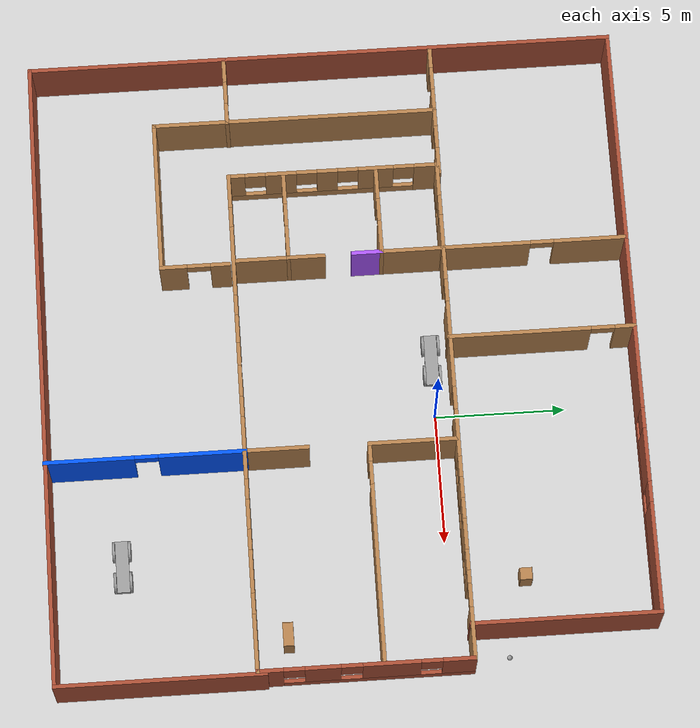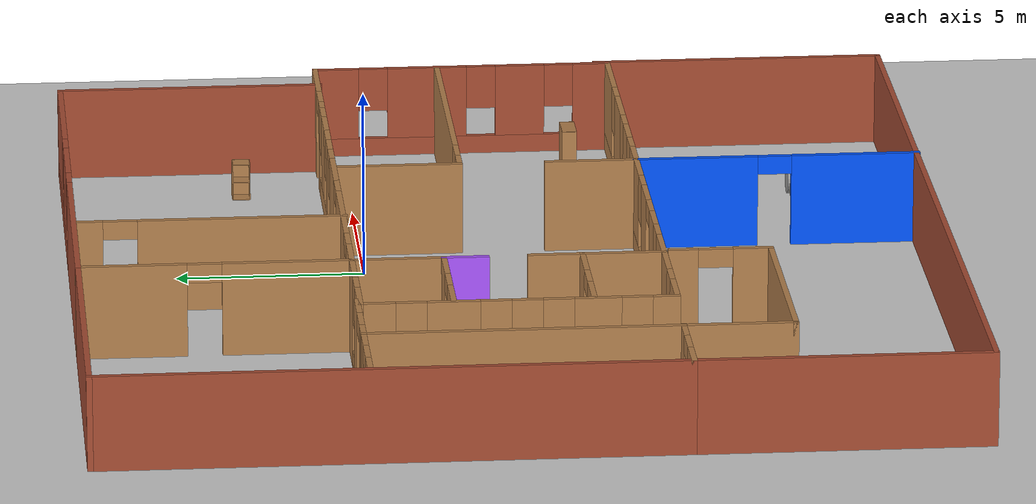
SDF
<sdf version="1.6">
 <world name="default">
  <plugin name="hello" filename="libhello.so"/>
  <light name="sun" type="directional">
   <pose>0 0 10 0 -0 0</pose>
   <diffuse>0.8 0.8 0.8 1</diffuse>
   <specular>0.2 0.2 0.2 1</specular>
   <attenuation>
    <range>1000</range>
    <constant>0.9</constant>
    <linear>0.01</linear>
    <quadratic>0.001</quadratic>
   </attenuation>
   <direction>-0.5 0.1 -0.9</direction>
  </light>
  <model name="ground_plane">
   <static>1</static>
   <link name="link">
    <collision name="collision">
     <geometry><plane><normal>0 0 1</normal><size>100 100</size></plane></geometry>
     <surface>
      <contact><collide_bitmask>65535</collide_bitmask></contact>
      <friction><ode><mu>100</mu><mu2>50</mu2></ode></friction>
     </surface>
    </collision>
    <visual name="visual">
     <cast_shadows>0</cast_shadows>
     <geometry><plane><normal>0 0 1</normal><size>100 100</size></plane></geometry>
     <material>
      <script><uri>file://media/materials/scripts/gazebo.material</uri><name>Gazebo/Grey</name></script>
     </material>
    </visual>
   </link>
  </model>
  <gravity>0 0 -9.8</gravity>
  <magnetic_field>6e-06 2.3e-05 -4.2e-05</magnetic_field>
  <atmosphere type="adiabatic"/>
  <physics name="default_physics" default="0" type="ode">
   <max_step_size>0.001</max_step_size>
   <real_time_factor>1</real_time_factor>
   <real_time_update_rate>1000</real_time_update_rate>
  </physics>
  <scene><ambient>0.4 0.4 0.4 1</ambient><background>0.7 0.7 0.7 1</background><shadows>1</shadows></scene>
  <spherical_coordinates>
   <surface_model>EARTH_WGS84</surface_model>
   <latitude_deg>0</latitude_deg>
   <longitude_deg>0</longitude_deg>
   <elevation>0</elevation>
   <heading_deg>0</heading_deg>
  </spherical_coordinates>
  <model name="RC">
   <link name="link_0">
    <inertial>
     <mass>1</mass>
     <inertia>
      <ixx>0.166667</ixx>
      <ixy>0</ixy>
      <ixz>0</ixz>
      <iyy>0.166667</iyy>
      <iyz>0</iyz>
      <izz>0.166667</izz>
     </inertia>
    </inertial>
    <visual name="visual">
     <geometry><box><size>2 0.5 0.2</size></box></geometry>
     <material>
      <lighting>1</lighting>
      <script><uri>file://media/materials/scripts/gazebo.material</uri><name>Gazebo/Grey</name></script>
      <shader type="pixel"><normal_map>__default__</normal_map></shader>
      <ambient>0.3 0.3 0.3 1</ambient>
      <diffuse>0.7 0.7 0.7 1</diffuse>
      <specular>0.01 0.01 0.01 1</specular>
      <emissive>0 0 0 1</emissive>
     </material>
    </visual>
    <collision name="collision">
     <geometry><box><size>2 0.5 0.2</size></box></geometry>
     <surface>
      <friction>
       <ode><mu>1</mu><mu2>1</mu2><fdir1>0 0 0</fdir1><slip1>0</slip1><slip2>0</slip2></ode>
       <torsional>
        <coefficient>1</coefficient>
        <patch_radius>0</patch_radius>
        <surface_radius>0</surface_radius>
        <use_patch_radius>1</use_patch_radius>
        <ode><slip>0</slip></ode>
       </torsional>
      </friction>
      <bounce><restitution_coefficient>0</restitution_coefficient><threshold>1e+06</threshold></bounce>
      <contact>
       <collide_without_contact>0</collide_without_contact>
       <collide_without_contact_bitmask>1</collide_without_contact_bitmask>
       <collide_bitmask>1</collide_bitmask>
       <ode>
        <soft_cfm>0</soft_cfm>
        <soft_erp>0.2</soft_erp>
        <kp>1e+13</kp>
        <kd>1</kd>
        <max_vel>0.01</max_vel>
        <min_depth>0</min_depth>
       </ode>
       <bullet>
        <split_impulse>1</split_impulse>
        <split_impulse_penetration_threshold>-0.01</split_impulse_penetration_threshold>
        <soft_cfm>0</soft_cfm>
        <soft_erp>0.2</soft_erp>
        <kp>1e+13</kp>
        <kd>1</kd>
       </bullet>
      </contact>
     </surface>
    </collision>
   </link>
   <link name="link_1">
    <pose>-0.6 -0.300039 0 1.5707 -0 0</pose>
    <inertial>
     <mass>1</mass>
     <inertia><ixx>0.145833</ixx><ixy>0</ixy><ixz>0</ixz><iyy>0.145833</iyy><iyz>0</iyz><izz>0.125</izz></inertia>
    </inertial>
    <visual name="visual">
     <geometry><cylinder><radius>0.4</radius><length>0.1</length></cylinder></geometry>
     <material>
      <lighting>1</lighting>
      <script><uri>file://media/materials/scripts/gazebo.material</uri><name>Gazebo/Grey</name></script>
      <shader type="pixel"><normal_map>__default__</normal_map></shader>
      <ambient>0.3 0.3 0.3 1</ambient>
      <diffuse>0.7 0.7 0.7 1</diffuse>
      <specular>0.01 0.01 0.01 1</specular>
      <emissive>0 0 0 1</emissive>
     </material>
    </visual>
    <collision name="collision">
     <geometry><cylinder><radius>0.4</radius><length>0.1</length></cylinder></geometry>
     <surface>
      <friction>
       <ode><mu>1</mu><mu2>1</mu2><fdir1>0 0 0</fdir1><slip1>0</slip1><slip2>0</slip2></ode>
       <torsional>
        <coefficient>1</coefficient>
        <patch_radius>0</patch_radius>
        <surface_radius>0</surface_radius>
        <use_patch_radius>1</use_patch_radius>
        <ode><slip>0</slip></ode>
       </torsional>
      </friction>
      <bounce><restitution_coefficient>0</restitution_coefficient><threshold>1e+06</threshold></bounce>
      <contact>
       <collide_without_contact>0</collide_without_contact>
       <collide_without_contact_bitmask>1</collide_without_contact_bitmask>
       <collide_bitmask>1</collide_bitmask>
       <ode>
        <soft_cfm>0</soft_cfm>
        <soft_erp>0.2</soft_erp>
        <kp>1e+13</kp>
        <kd>1</kd>
        <max_vel>0.01</max_vel>
        <min_depth>0</min_depth>
       </ode>
       <bullet>
        <split_impulse>1</split_impulse>
        <split_impulse_penetration_threshold>-0.01</split_impulse_penetration_threshold>
        <soft_cfm>0</soft_cfm>
        <soft_erp>0.2</soft_erp>
        <kp>1e+13</kp>
        <kd>1</kd>
       </bullet>
      </contact>
     </surface>
    </collision>
   </link>
   <link name="link_1_clone">
    <pose>-0.6 0.300039 0 1.5707 -0 0</pose>
    <inertial>
     <mass>1</mass>
     <inertia><ixx>0.145833</ixx><ixy>0</ixy><ixz>0</ixz><iyy>0.145833</iyy><iyz>0</iyz><izz>0.125</izz></inertia>
    </inertial>
    <visual name="visual">
     <geometry><cylinder><radius>0.4</radius><length>0.1</length></cylinder></geometry>
     <material>
      <lighting>1</lighting>
      <script><uri>file://media/materials/scripts/gazebo.material</uri><name>Gazebo/Grey</name></script>
      <shader type="pixel"><normal_map>__default__</normal_map></shader>
      <ambient>0.3 0.3 0.3 1</ambient>
      <diffuse>0.7 0.7 0.7 1</diffuse>
      <specular>0.01 0.01 0.01 1</specular>
      <emissive>0 0 0 1</emissive>
     </material>
    </visual>
    <collision name="collision">
     <geometry><cylinder><radius>0.4</radius><length>0.1</length></cylinder></geometry>
     <surface>
      <friction>
       <ode><mu>1</mu><mu2>1</mu2><fdir1>0 0 0</fdir1><slip1>0</slip1><slip2>0</slip2></ode>
       <torsional>
        <coefficient>1</coefficient>
        <patch_radius>0</patch_radius>
        <surface_radius>0</surface_radius>
        <use_patch_radius>1</use_patch_radius>
        <ode><slip>0</slip></ode>
       </torsional>
      </friction>
      <bounce><restitution_coefficient>0</restitution_coefficient><threshold>1e+06</threshold></bounce>
      <contact>
       <collide_without_contact>0</collide_without_contact>
       <collide_without_contact_bitmask>1</collide_without_contact_bitmask>
       <collide_bitmask>1</collide_bitmask>
       <ode>
        <soft_cfm>0</soft_cfm>
        <soft_erp>0.2</soft_erp>
        <kp>1e+13</kp>
        <kd>1</kd>
        <max_vel>0.01</max_vel>
        <min_depth>0</min_depth>
       </ode>
       <bullet>
        <split_impulse>1</split_impulse>
        <split_impulse_penetration_threshold>-0.01</split_impulse_penetration_threshold>
        <soft_cfm>0</soft_cfm>
        <soft_erp>0.2</soft_erp>
        <kp>1e+13</kp>
        <kd>1</kd>
       </bullet>
      </contact>
     </surface>
    </collision>
   </link>
   <link name="link_1_clone_0">
    <pose>0.6 -0.300039 0 1.5707 -0 0</pose>
    <inertial>
     <mass>1</mass>
     <inertia><ixx>0.145833</ixx><ixy>0</ixy><ixz>0</ixz><iyy>0.145833</iyy><iyz>0</iyz><izz>0.125</izz></inertia>
    </inertial>
    <visual name="visual">
     <geometry><cylinder><radius>0.4</radius><length>0.1</length></cylinder></geometry>
     <material>
      <lighting>1</lighting>
      <script><uri>file://media/materials/scripts/gazebo.material</uri><name>Gazebo/Grey</name></script>
      <shader type="pixel"><normal_map>__default__</normal_map></shader>
      <ambient>0.3 0.3 0.3 1</ambient>
      <diffuse>0.7 0.7 0.7 1</diffuse>
      <specular>0.01 0.01 0.01 1</specular>
      <emissive>0 0 0 1</emissive>
     </material>
    </visual>
    <collision name="collision">
     <geometry><cylinder><radius>0.4</radius><length>0.1</length></cylinder></geometry>
     <surface>
      <friction>
       <ode><mu>1</mu><mu2>1</mu2><fdir1>0 0 0</fdir1><slip1>0</slip1><slip2>0</slip2></ode>
       <torsional>
        <coefficient>1</coefficient>
        <patch_radius>0</patch_radius>
        <surface_radius>0</surface_radius>
        <use_patch_radius>1</use_patch_radius>
        <ode><slip>0</slip></ode>
       </torsional>
      </friction>
      <bounce><restitution_coefficient>0</restitution_coefficient><threshold>1e+06</threshold></bounce>
      <contact>
       <collide_without_contact>0</collide_without_contact>
       <collide_without_contact_bitmask>1</collide_without_contact_bitmask>
       <collide_bitmask>1</collide_bitmask>
       <ode>
        <soft_cfm>0</soft_cfm>
        <soft_erp>0.2</soft_erp>
        <kp>1e+13</kp>
        <kd>1</kd>
        <max_vel>0.01</max_vel>
        <min_depth>0</min_depth>
       </ode>
       <bullet>
        <split_impulse>1</split_impulse>
        <split_impulse_penetration_threshold>-0.01</split_impulse_penetration_threshold>
        <soft_cfm>0</soft_cfm>
        <soft_erp>0.2</soft_erp>
        <kp>1e+13</kp>
        <kd>1</kd>
       </bullet>
      </contact>
     </surface>
    </collision>
   </link>
   <link name="link_1_clone_1">
    <pose>0.6 0.300039 0 1.5707 -0 0</pose>
    <inertial>
     <mass>1</mass>
     <inertia><ixx>0.145833</ixx><ixy>0</ixy><ixz>0</ixz><iyy>0.145833</iyy><iyz>0</iyz><izz>0.125</izz></inertia>
    </inertial>
    <visual name="visual">
     <geometry><cylinder><radius>0.4</radius><length>0.1</length></cylinder></geometry>
     <material>
      <lighting>1</lighting>
      <script><uri>file://media/materials/scripts/gazebo.material</uri><name>Gazebo/Grey</name></script>
      <shader type="pixel"><normal_map>__default__</normal_map></shader>
      <ambient>0.3 0.3 0.3 1</ambient>
      <diffuse>0.7 0.7 0.7 1</diffuse>
      <specular>0.01 0.01 0.01 1</specular>
      <emissive>0 0 0 1</emissive>
     </material>
    </visual>
    <collision name="collision">
     <geometry><cylinder><radius>0.4</radius><length>0.1</length></cylinder></geometry>
     <surface>
      <friction>
       <ode><mu>1</mu><mu2>1</mu2><fdir1>0 0 0</fdir1><slip1>0</slip1><slip2>0</slip2></ode>
       <torsional>
        <coefficient>1</coefficient>
        <patch_radius>0</patch_radius>
        <surface_radius>0</surface_radius>
        <use_patch_radius>1</use_patch_radius>
        <ode><slip>0</slip></ode>
       </torsional>
      </friction>
      <bounce><restitution_coefficient>0</restitution_coefficient><threshold>1e+06</threshold></bounce>
      <contact>
       <collide_without_contact>0</collide_without_contact>
       <collide_without_contact_bitmask>1</collide_without_contact_bitmask>
       <collide_bitmask>1</collide_bitmask>
       <ode>
        <soft_cfm>0</soft_cfm>
        <soft_erp>0.2</soft_erp>
        <kp>1e+13</kp>
        <kd>1</kd>
        <max_vel>0.01</max_vel>
        <min_depth>0</min_depth>
       </ode>
       <bullet>
        <split_impulse>1</split_impulse>
        <split_impulse_penetration_threshold>-0.01</split_impulse_penetration_threshold>
        <soft_cfm>0</soft_cfm>
        <soft_erp>0.2</soft_erp>
        <kp>1e+13</kp>
        <kd>1</kd>
       </bullet>
      </contact>
     </surface>
    </collision>
   </link>
   <joint name="link_0_JOINT_6" type="revolute">
    <parent>link_0</parent>
    <child>link_1_clone_1</child>
    <axis>
     <xyz>0 0 -1</xyz>
     <use_parent_model_frame>0</use_parent_model_frame>
     <limit>
      <lower>-1.79769e+308</lower>
      <upper>1.79769e+308</upper>
      <effort>-1</effort>
      <velocity>-1</velocity>
     </limit>
     <dynamics>
      <spring_reference>0</spring_reference>
      <spring_stiffness>0</spring_stiffness>
      <damping>0</damping>
     </dynamics>
    </axis>
    <physics>
     <ode><limit><cfm>0</cfm><erp>0.2</erp></limit><suspension><cfm>0</cfm><erp>0.2</erp></suspension></ode>
    </physics>
   </joint>
   <joint name="link_0_JOINT_7" type="revolute">
    <parent>link_0</parent>
    <child>link_1_clone</child>
    <axis>
     <xyz>0 0 -1</xyz>
     <use_parent_model_frame>0</use_parent_model_frame>
     <limit>
      <lower>-1.79769e+308</lower>
      <upper>1.79769e+308</upper>
      <effort>-1</effort>
      <velocity>-1</velocity>
     </limit>
     <dynamics>
      <spring_reference>0</spring_reference>
      <spring_stiffness>0</spring_stiffness>
      <damping>0</damping>
     </dynamics>
    </axis>
    <physics>
     <ode><limit><cfm>0</cfm><erp>0.2</erp></limit><suspension><cfm>0</cfm><erp>0.2</erp></suspension></ode>
    </physics>
   </joint>
   <joint name="link_0_JOINT_8" type="revolute">
    <parent>link_0</parent>
    <child>link_1_clone_0</child>
    <axis>
     <xyz>0 0 1</xyz>
     <use_parent_model_frame>0</use_parent_model_frame>
     <limit>
      <lower>-1.79769e+308</lower>
      <upper>1.79769e+308</upper>
      <effort>-1</effort>
      <velocity>-1</velocity>
     </limit>
     <dynamics>
      <spring_reference>0</spring_reference>
      <spring_stiffness>0</spring_stiffness>
      <damping>0</damping>
     </dynamics>
    </axis>
    <physics>
     <ode><limit><cfm>0</cfm><erp>0.2</erp></limit><suspension><cfm>0</cfm><erp>0.2</erp></suspension></ode>
    </physics>
   </joint>
   <joint name="link_0_JOINT_9" type="revolute">
    <parent>link_0</parent>
    <child>link_1</child>
    <axis>
     <xyz>0 0 1</xyz>
     <use_parent_model_frame>0</use_parent_model_frame>
     <limit>
      <lower>-1.79769e+308</lower>
      <upper>1.79769e+308</upper>
      <effort>-1</effort>
      <velocity>-1</velocity>
     </limit>
     <dynamics>
      <spring_reference>0</spring_reference>
      <spring_stiffness>0</spring_stiffness>
      <damping>0</damping>
     </dynamics>
    </axis>
    <physics>
     <ode><limit><cfm>0</cfm><erp>0.2</erp></limit><suspension><cfm>0</cfm><erp>0.2</erp></suspension></ode>
    </physics>
   </joint>
   <static>0</static>
   <pose>-2.18691 0.000323 0.400005 -1e-06 0 -4.2e-05</pose>
  </model>
  <model name="Building">
   <pose>-2.11328 -3.59888 0 0 -0 0</pose>
   <link name="Wall_10">
    <pose>-5.625 1.91472 0 0 -0 3.14159</pose>
    <visual name="Wall_10_Visual_0">
     <pose>-1.07415 0 1.25 0 -0 0</pose>
     <geometry><box><size>1.35171 0.15 2.5</size></box></geometry>
     <material>
      <script><uri>file://media/materials/scripts/gazebo.material</uri><name>Gazebo/Wood</name></script>
      <ambient>1 1 1 1</ambient>
     </material>
     <meta><layer>0</layer></meta>
    </visual>
    <collision name="Wall_10_Collision_0">
     <geometry><box><size>1.35171 0.15 2.5</size></box></geometry>
     <pose>-1.07415 0 1.25 0 -0 0</pose>
    </collision>
    <visual name="Wall_10_Visual_1">
     <pose>1.12585 0 1.25 0 -0 0</pose>
     <geometry><box><size>1.24829 0.15 2.5</size></box></geometry>
     <material>
      <script><uri>file://media/materials/scripts/gazebo.material</uri><name>Gazebo/Wood</name></script>
      <ambient>1 1 1 1</ambient>
     </material>
     <meta><layer>0</layer></meta>
    </visual>
    <collision name="Wall_10_Collision_1">
     <geometry><box><size>1.24829 0.15 2.5</size></box></geometry>
     <pose>1.12585 0 1.25 0 -0 0</pose>
    </collision>
    <visual name="Wall_10_Visual_2">
     <pose>0.051708 0 2.25 0 -0 0</pose>
     <geometry><box><size>0.9 0.15 0.5</size></box></geometry>
     <material>
      <script><uri>file://media/materials/scripts/gazebo.material</uri><name>Gazebo/Wood</name></script>
      <ambient>1 1 1 1</ambient>
     </material>
     <meta><layer>0</layer></meta>
    </visual>
    <collision name="Wall_10_Collision_2">
     <geometry><box><size>0.9 0.15 0.5</size></box></geometry>
     <pose>0.051708 0 2.25 0 -0 0</pose>
    </collision>
   </link>
   <link name="Wall_12">
    <pose>-5.60058 -1.67887 0 0 -0 0</pose>
    <visual name="Wall_12_Visual_0">
     <pose>-1.13806 0 1.25 0 -0 0</pose>
     <geometry><box><size>1.22387 0.15 2.5</size></box></geometry>
     <material>
      <script><uri>file://media/materials/scripts/gazebo.material</uri><name>Gazebo/Wood</name></script>
      <ambient>1 1 1 1</ambient>
     </material>
     <meta><layer>0</layer></meta>
    </visual>
    <collision name="Wall_12_Collision_0">
     <geometry><box><size>1.22387 0.15 2.5</size></box></geometry>
     <pose>-1.13806 0 1.25 0 -0 0</pose>
    </collision>
    <visual name="Wall_12_Visual_1">
     <pose>1.06194 0 1.25 0 -0 0</pose>
     <geometry><box><size>1.37613 0.15 2.5</size></box></geometry>
     <material>
      <script><uri>file://media/materials/scripts/gazebo.material</uri><name>Gazebo/Wood</name></script>
      <ambient>1 1 1 1</ambient>
     </material>
     <meta><layer>0</layer></meta>
    </visual>
    <collision name="Wall_12_Collision_1">
     <geometry><box><size>1.37613 0.15 2.5</size></box></geometry>
     <pose>1.06194 0 1.25 0 -0 0</pose>
    </collision>
    <visual name="Wall_12_Visual_2">
     <pose>-0.076126 0 2.25 0 -0 0</pose>
     <geometry><box><size>0.9 0.15 0.5</size></box></geometry>
     <material>
      <script><uri>file://media/materials/scripts/gazebo.material</uri><name>Gazebo/Wood</name></script>
      <ambient>1 1 1 1</ambient>
     </material>
     <meta><layer>0</layer></meta>
    </visual>
    <collision name="Wall_12_Collision_2">
     <geometry><box><size>0.9 0.15 0.5</size></box></geometry>
     <pose>-0.076126 0 2.25 0 -0 0</pose>
    </collision>
   </link>
   <link name="Wall_13">
    <collision name="Wall_13_Collision">
     <geometry><box><size>2.25 0.15 2.5</size></box></geometry>
     <pose>0 0 1.25 0 -0 0</pose>
    </collision>
    <visual name="Wall_13_Visual">
     <pose>0 0 1.25 0 -0 0</pose>
     <geometry><box><size>2.25 0.15 2.5</size></box></geometry>
     <material>
      <script><uri>file://media/materials/scripts/gazebo.material</uri><name>Gazebo/Wood</name></script>
      <ambient>1 1 1 1</ambient>
     </material>
     <meta><layer>0</layer></meta>
    </visual>
    <pose>-3.92558 -2.72887 0 0 0 -1.5708</pose>
   </link>
   <link name="Wall_15">
    <collision name="Wall_15_Collision">
     <geometry><box><size>1.5 0.15 2.5</size></box></geometry>
     <pose>0 0 1.25 0 -0 0</pose>
    </collision>
    <visual name="Wall_15_Visual">
     <pose>0 0 1.25 0 -0 0</pose>
     <geometry><box><size>1.5 0.15 2.5</size></box></geometry>
     <material>
      <script><uri>file://media/materials/scripts/gazebo.material</uri><name>Gazebo/Wood</name></script>
      <ambient>0.666667 0.333333 1 1</ambient>
     </material>
     <meta><layer>0</layer></meta>
    </visual>
    <pose>-3.92558 -1.00387 0 0 -0 1.5708</pose>
   </link>
   <link name="Wall_17">
    <collision name="Wall_17_Collision">
     <geometry><box><size>1.25 0.15 2.5</size></box></geometry>
     <pose>0 0 1.25 0 -0 0</pose>
    </collision>
    <visual name="Wall_17_Visual">
     <pose>0 0 1.25 0 -0 0</pose>
     <geometry><box><size>1.25 0.15 2.5</size></box></geometry>
     <material>
      <script><uri>file://media/materials/scripts/gazebo.material</uri><name>Gazebo/Grey</name></script>
      <ambient>0.666667 0.333333 1 1</ambient>
     </material>
     <meta><layer>0</layer></meta>
    </visual>
    <pose>-3.95 1.36472 0 0 0 -1.5708</pose>
   </link>
   <link name="Wall_19">
    <collision name="Wall_19_Collision">
     <geometry><box><size>3.5 0.15 2.5</size></box></geometry>
     <pose>0 0 1.25 0 -0 0</pose>
    </collision>
    <visual name="Wall_19_Visual">
     <pose>0 0 1.25 0 -0 0</pose>
     <geometry><box><size>3.5 0.15 2.5</size></box></geometry>
     <material>
      <script><uri>file://media/materials/scripts/gazebo.material</uri><name>Gazebo/Wood</name></script>
      <ambient>1 1 1 1</ambient>
     </material>
     <meta><layer>0</layer></meta>
    </visual>
    <pose>3.70447 2.60682 0 0 0 -1.5708</pose>
   </link>
   <link name="Wall_20">
    <pose>7.87947 0.931819 0 0 -0 0</pose>
    <visual name="Wall_20_Visual_0">
     <pose>-3.86745 0 1.25 0 -0 0</pose>
     <geometry><box><size>0.765092 0.15 2.5</size></box></geometry>
     <material>
      <script><uri>file://media/materials/scripts/gazebo.material</uri><name>Gazebo/Wood</name></script>
      <ambient>1 1 1 1</ambient>
     </material>
     <meta><layer>0</layer></meta>
    </visual>
    <collision name="Wall_20_Collision_0">
     <geometry><box><size>0.765092 0.15 2.5</size></box></geometry>
     <pose>-3.86745 0 1.25 0 -0 0</pose>
    </collision>
    <visual name="Wall_20_Visual_1">
     <pose>0.832546 0 1.25 0 -0 0</pose>
     <geometry><box><size>6.83491 0.15 2.5</size></box></geometry>
     <material>
      <script><uri>file://media/materials/scripts/gazebo.material</uri><name>Gazebo/Wood</name></script>
      <ambient>1 1 1 1</ambient>
     </material>
     <meta><layer>0</layer></meta>
    </visual>
    <collision name="Wall_20_Collision_1">
     <geometry><box><size>6.83491 0.15 2.5</size></box></geometry>
     <pose>0.832546 0 1.25 0 -0 0</pose>
    </collision>
    <visual name="Wall_20_Visual_2">
     <pose>-3.03491 0 2.25 0 -0 0</pose>
     <geometry><box><size>0.9 0.15 0.5</size></box></geometry>
     <material>
      <script><uri>file://media/materials/scripts/gazebo.material</uri><name>Gazebo/Wood</name></script>
      <ambient>1 1 1 1</ambient>
     </material>
     <meta><layer>0</layer></meta>
    </visual>
    <collision name="Wall_20_Collision_2">
     <geometry><box><size>0.9 0.15 0.5</size></box></geometry>
     <pose>-3.03491 0 2.25 0 -0 0</pose>
    </collision>
   </link>
   <link name="Wall_22">
    <collision name="Wall_22_Collision">
     <geometry><box><size>2.5 0.15 2.5</size></box></geometry>
     <pose>0 0 1.25 0 -0 0</pose>
    </collision>
    <visual name="Wall_22_Visual">
     <pose>0 0 1.25 0 -0 0</pose>
     <geometry><box><size>2.5 0.15 2.5</size></box></geometry>
     <material>
      <script><uri>file://media/materials/scripts/gazebo.material</uri><name>Gazebo/Wood</name></script>
      <ambient>1 1 1 1</ambient>
     </material>
     <meta><layer>0</layer></meta>
    </visual>
    <pose>3.68886 -2.58973 0 0 -0 1.5708</pose>
   </link>
   <link name="Wall_24">
    <pose>-3.95 7.81472 0 0 -0 1.5708</pose>
    <visual name="Wall_24_Visual_0">
     <pose>-1.89111 0 1.25 0 -0 0</pose>
     <geometry><box><size>3.46777 0.15 2.5</size></box></geometry>
     <material>
      <script><uri>file://media/materials/scripts/gazebo.material</uri><name>Gazebo/Wood</name></script>
      <ambient>1 1 1 1</ambient>
     </material>
     <meta><layer>0</layer></meta>
    </visual>
    <collision name="Wall_24_Collision_0">
     <geometry><box><size>3.46777 0.15 2.5</size></box></geometry>
     <pose>-1.89111 0 1.25 0 -0 0</pose>
    </collision>
    <visual name="Wall_24_Visual_1">
     <pose>2.18389 0 1.25 0 -0 0</pose>
     <geometry><box><size>2.88223 0.15 2.5</size></box></geometry>
     <material>
      <script><uri>file://media/materials/scripts/gazebo.material</uri><name>Gazebo/Wood</name></script>
      <ambient>1 1 1 1</ambient>
     </material>
     <meta><layer>0</layer></meta>
    </visual>
    <collision name="Wall_24_Collision_1">
     <geometry><box><size>2.88223 0.15 2.5</size></box></geometry>
     <pose>2.18389 0 1.25 0 -0 0</pose>
    </collision>
    <visual name="Wall_24_Visual_2">
     <pose>0.292772 0 2.25 0 -0 0</pose>
     <geometry><box><size>0.9 0.15 0.5</size></box></geometry>
     <material>
      <script><uri>file://media/materials/scripts/gazebo.material</uri><name>Gazebo/Wood</name></script>
      <ambient>1 1 1 1</ambient>
     </material>
     <meta><layer>0</layer></meta>
    </visual>
    <collision name="Wall_24_Collision_2">
     <geometry><box><size>0.9 0.15 0.5</size></box></geometry>
     <pose>0.292772 0 2.25 0 -0 0</pose>
    </collision>
   </link>
   <link name="Wall_25">
    <pose>3.475 11.3647 0 0 -0 0</pose>
    <visual name="Wall_25_Visual_0">
     <pose>-4.00983 0 1.25 0 -0 0</pose>
     <geometry><box><size>6.98034 0.15 2.5</size></box></geometry>
     <material>
      <script><uri>file://media/materials/scripts/gazebo.material</uri><name>Gazebo/Bricks</name></script>
      <ambient>0 0.333333 1 1</ambient>
     </material>
     <meta><layer>0</layer></meta>
    </visual>
    <collision name="Wall_25_Collision_0">
     <geometry><box><size>6.98034 0.15 2.5</size></box></geometry>
     <pose>-4.00983 0 1.25 0 -0 0</pose>
    </collision>
    <visual name="Wall_25_Visual_1">
     <pose>3.49017 0 0.25 0 -0 0</pose>
     <geometry><box><size>8.01966 0.15 0.5</size></box></geometry>
     <material>
      <script><uri>file://media/materials/scripts/gazebo.material</uri><name>Gazebo/Bricks</name></script>
      <ambient>0 0.333333 1 1</ambient>
     </material>
     <meta><layer>0</layer></meta>
    </visual>
    <collision name="Wall_25_Collision_1">
     <geometry><box><size>8.01966 0.15 0.5</size></box></geometry>
     <pose>3.49017 0 0.25 0 -0 0</pose>
    </collision>
    <visual name="Wall_25_Visual_2">
     <pose>1.32873 0 1.5 0 -0 0</pose>
     <geometry><box><size>2.09676 0.15 2</size></box></geometry>
     <material>
      <script><uri>file://media/materials/scripts/gazebo.material</uri><name>Gazebo/Bricks</name></script>
      <ambient>0 0.333333 1 1</ambient>
     </material>
     <meta><layer>0</layer></meta>
    </visual>
    <collision name="Wall_25_Collision_2">
     <geometry><box><size>2.09676 0.15 2</size></box></geometry>
     <pose>1.32873 0 1.5 0 -0 0</pose>
    </collision>
    <visual name="Wall_25_Visual_3">
     <pose>5.33856 0 1.5 0 -0 0</pose>
     <geometry><box><size>4.32289 0.15 2</size></box></geometry>
     <material>
      <script><uri>file://media/materials/scripts/gazebo.material</uri><name>Gazebo/Bricks</name></script>
      <ambient>0 0.333333 1 1</ambient>
     </material>
     <meta><layer>0</layer></meta>
    </visual>
    <collision name="Wall_25_Collision_3">
     <geometry><box><size>4.32289 0.15 2</size></box></geometry>
     <pose>5.33856 0 1.5 0 -0 0</pose>
    </collision>
    <visual name="Wall_25_Visual_4">
     <pose>-0.119655 0 1.9 0 -0 0</pose>
     <geometry><box><size>0.8 0.15 1.2</size></box></geometry>
     <material>
      <script><uri>file://media/materials/scripts/gazebo.material</uri><name>Gazebo/Bricks</name></script>
      <ambient>0 0.333333 1 1</ambient>
     </material>
     <meta><layer>0</layer></meta>
    </visual>
    <collision name="Wall_25_Collision_4">
     <geometry><box><size>0.8 0.15 1.2</size></box></geometry>
     <pose>-0.119655 0 1.9 0 -0 0</pose>
    </collision>
    <visual name="Wall_25_Visual_5">
     <pose>2.77711 0 1.9 0 -0 0</pose>
     <geometry><box><size>0.8 0.15 1.2</size></box></geometry>
     <material>
      <script><uri>file://media/materials/scripts/gazebo.material</uri><name>Gazebo/Bricks</name></script>
      <ambient>0 0.333333 1 1</ambient>
     </material>
     <meta><layer>0</layer></meta>
    </visual>
    <collision name="Wall_25_Collision_5">
     <geometry><box><size>0.8 0.15 1.2</size></box></geometry>
     <pose>2.77711 0 1.9 0 -0 0</pose>
    </collision>
   </link>
   <link name="Wall_28">
    <pose>-0.342826 7.80635 0 0 -0 1.5708</pose>
    <visual name="Wall_28_Visual_0">
     <pose>-0.866599 0 1.25 0 -0 0</pose>
     <geometry><box><size>5.5168 0.15 2.5</size></box></geometry>
     <material>
      <script><uri>file://media/materials/scripts/gazebo.material</uri><name>Gazebo/Wood</name></script>
      <ambient>1 1 1 1</ambient>
     </material>
     <meta><layer>0</layer></meta>
    </visual>
    <collision name="Wall_28_Collision_0">
     <geometry><box><size>5.5168 0.15 2.5</size></box></geometry>
     <pose>-0.866599 0 1.25 0 -0 0</pose>
    </collision>
    <visual name="Wall_28_Visual_1">
     <pose>3.2084 0 1.25 0 -0 0</pose>
     <geometry><box><size>0.833197 0.15 2.5</size></box></geometry>
     <material>
      <script><uri>file://media/materials/scripts/gazebo.material</uri><name>Gazebo/Wood</name></script>
      <ambient>1 1 1 1</ambient>
     </material>
     <meta><layer>0</layer></meta>
    </visual>
    <collision name="Wall_28_Collision_1">
     <geometry><box><size>0.833197 0.15 2.5</size></box></geometry>
     <pose>3.2084 0 1.25 0 -0 0</pose>
    </collision>
    <visual name="Wall_28_Visual_2">
     <pose>2.3418 0 2.25 0 -0 0</pose>
     <geometry><box><size>0.9 0.15 0.5</size></box></geometry>
     <material>
      <script><uri>file://media/materials/scripts/gazebo.material</uri><name>Gazebo/Wood</name></script>
      <ambient>1 1 1 1</ambient>
     </material>
     <meta><layer>0</layer></meta>
    </visual>
    <collision name="Wall_28_Collision_2">
     <geometry><box><size>0.9 0.15 0.5</size></box></geometry>
     <pose>2.3418 0 2.25 0 -0 0</pose>
    </collision>
   </link>
   <link name="Wall_30">
    <collision name="Wall_30_Collision">
     <geometry><box><size>7.25 0.15 2.5</size></box></geometry>
     <pose>0 0 1.25 0 -0 0</pose>
    </collision>
    <visual name="Wall_30_Visual">
     <pose>0 0 1.25 0 -0 0</pose>
     <geometry><box><size>7.25 0.15 2.5</size></box></geometry>
     <material>
      <script><uri>file://media/materials/scripts/gazebo.material</uri><name>Gazebo/Bricks</name></script>
      <ambient>0 0.333333 1 1</ambient>
     </material>
     <meta><layer>0</layer></meta>
    </visual>
    <pose>10.9 7.81472 0 0 0 -1.5708</pose>
   </link>
   <link name="Wall_32">
    <collision name="Wall_32_Collision">
     <geometry><box><size>8.5 0.15 2.5</size></box></geometry>
     <pose>0 0 1.25 0 -0 0</pose>
    </collision>
    <visual name="Wall_32_Visual">
     <pose>0 0 1.25 0 -0 0</pose>
     <geometry><box><size>8.5 0.15 2.5</size></box></geometry>
     <material>
      <script><uri>file://media/materials/scripts/gazebo.material</uri><name>Gazebo/Bricks</name></script>
      <ambient>0 0.333333 1 1</ambient>
     </material>
     <meta><layer>0</layer></meta>
    </visual>
    <pose>-8.125 11.3647 0 0 -0 3.14159</pose>
   </link>
   <link name="Wall_33">
    <collision name="Wall_33_Collision">
     <geometry><box><size>15.25 0.15 2.5</size></box></geometry>
     <pose>0 0 1.25 0 -0 0</pose>
    </collision>
    <visual name="Wall_33_Visual">
     <pose>0 0 1.25 0 -0 0</pose>
     <geometry><box><size>15.25 0.15 2.5</size></box></geometry>
     <material>
      <script><uri>file://media/materials/scripts/gazebo.material</uri><name>Gazebo/Bricks</name></script>
      <ambient>0 0.333333 1 1</ambient>
     </material>
     <meta><layer>0</layer></meta>
    </visual>
    <pose>-12.3 3.81472 0 0 0 -1.5708</pose>
   </link>
   <link name="Wall_34">
    <pose>-10.9689 -3.73528 0 0 -0 0</pose>
    <visual name="Wall_34_Visual_0">
     <pose>-0.895229 0 1.25 0 -0 0</pose>
     <geometry><box><size>1.02177 0.15 2.5</size></box></geometry>
     <material>
      <script><uri>file://media/materials/scripts/gazebo.material</uri><name>Gazebo/Wood</name></script>
      <ambient>1 1 1 1</ambient>
     </material>
     <meta><layer>0</layer></meta>
    </visual>
    <collision name="Wall_34_Collision_0">
     <geometry><box><size>1.02177 0.15 2.5</size></box></geometry>
     <pose>-0.895229 0 1.25 0 -0 0</pose>
    </collision>
    <visual name="Wall_34_Visual_1">
     <pose>0.960885 0 1.25 0 -0 0</pose>
     <geometry><box><size>0.890458 0.15 2.5</size></box></geometry>
     <material>
      <script><uri>file://media/materials/scripts/gazebo.material</uri><name>Gazebo/Wood</name></script>
      <ambient>1 1 1 1</ambient>
     </material>
     <meta><layer>0</layer></meta>
    </visual>
    <collision name="Wall_34_Collision_1">
     <geometry><box><size>0.890458 0.15 2.5</size></box></geometry>
     <pose>0.960885 0 1.25 0 -0 0</pose>
    </collision>
    <visual name="Wall_34_Visual_2">
     <pose>0.065657 0 2.25 0 -0 0</pose>
     <geometry><box><size>0.9 0.15 0.5</size></box></geometry>
     <material>
      <script><uri>file://media/materials/scripts/gazebo.material</uri><name>Gazebo/Wood</name></script>
      <ambient>1 1 1 1</ambient>
     </material>
     <meta><layer>0</layer></meta>
    </visual>
    <collision name="Wall_34_Collision_2">
     <geometry><box><size>0.9 0.15 0.5</size></box></geometry>
     <pose>0.065657 0 2.25 0 -0 0</pose>
    </collision>
   </link>
   <link name="Wall_35">
    <collision name="Wall_35_Collision">
     <geometry><box><size>8.25 0.15 2.5</size></box></geometry>
     <pose>0 0 1.25 0 -0 0</pose>
    </collision>
    <visual name="Wall_35_Visual">
     <pose>0 0 1.25 0 -0 0</pose>
     <geometry><box><size>8.25 0.15 2.5</size></box></geometry>
     <material>
      <script><uri>file://media/materials/scripts/gazebo.material</uri><name>Gazebo/Wood</name></script>
      <ambient>1 1 1 1</ambient>
     </material>
     <meta><layer>0</layer></meta>
    </visual>
    <pose>-9.66889 0.314724 0 0 -0 1.5708</pose>
   </link>
   <link name="Wall_37">
    <pose>-8.36889 4.36472 0 0 -0 0</pose>
    <visual name="Wall_37_Visual_0">
     <pose>-0.997307 0 1.25 0 -0 0</pose>
     <geometry><box><size>0.755386 0.15 2.5</size></box></geometry>
     <material>
      <script><uri>file://media/materials/scripts/gazebo.material</uri><name>Gazebo/Wood</name></script>
      <ambient>1 1 1 1</ambient>
     </material>
     <meta><layer>0</layer></meta>
    </visual>
    <collision name="Wall_37_Collision_0">
     <geometry><box><size>0.755386 0.15 2.5</size></box></geometry>
     <pose>-0.997307 0 1.25 0 -0 0</pose>
    </collision>
    <visual name="Wall_37_Visual_1">
     <pose>0.827693 0 1.25 0 -0 0</pose>
     <geometry><box><size>1.09461 0.15 2.5</size></box></geometry>
     <material>
      <script><uri>file://media/materials/scripts/gazebo.material</uri><name>Gazebo/Wood</name></script>
      <ambient>1 1 1 1</ambient>
     </material>
     <meta><layer>0</layer></meta>
    </visual>
    <collision name="Wall_37_Collision_1">
     <geometry><box><size>1.09461 0.15 2.5</size></box></geometry>
     <pose>0.827693 0 1.25 0 -0 0</pose>
    </collision>
    <visual name="Wall_37_Visual_2">
     <pose>-0.169614 0 2.25 0 -0 0</pose>
     <geometry><box><size>0.9 0.15 0.5</size></box></geometry>
     <material>
      <script><uri>file://media/materials/scripts/gazebo.material</uri><name>Gazebo/Wood</name></script>
      <ambient>1 1 1 1</ambient>
     </material>
     <meta><layer>0</layer></meta>
    </visual>
    <collision name="Wall_37_Collision_2">
     <geometry><box><size>0.9 0.15 0.5</size></box></geometry>
     <pose>-0.169614 0 2.25 0 -0 0</pose>
    </collision>
   </link>
   <link name="Wall_39">
    <pose>-10.9689 4.36472 0 0 -0 3.14159</pose>
    <visual name="Wall_39_Visual_0">
     <pose>-0.897214 0 1.25 0 -0 0</pose>
     <geometry><box><size>0.955572 0.15 2.5</size></box></geometry>
     <material>
      <script><uri>file://media/materials/scripts/gazebo.material</uri><name>Gazebo/Wood</name></script>
      <ambient>1 1 1 1</ambient>
     </material>
     <meta><layer>0</layer></meta>
    </visual>
    <collision name="Wall_39_Collision_0">
     <geometry><box><size>0.955572 0.15 2.5</size></box></geometry>
     <pose>-0.897214 0 1.25 0 -0 0</pose>
    </collision>
    <visual name="Wall_39_Visual_1">
     <pose>0.927786 0 1.25 0 -0 0</pose>
     <geometry><box><size>0.894428 0.15 2.5</size></box></geometry>
     <material>
      <script><uri>file://media/materials/scripts/gazebo.material</uri><name>Gazebo/Wood</name></script>
      <ambient>1 1 1 1</ambient>
     </material>
     <meta><layer>0</layer></meta>
    </visual>
    <collision name="Wall_39_Collision_1">
     <geometry><box><size>0.894428 0.15 2.5</size></box></geometry>
     <pose>0.927786 0 1.25 0 -0 0</pose>
    </collision>
    <visual name="Wall_39_Visual_2">
     <pose>0.030572 0 2.25 0 -0 0</pose>
     <geometry><box><size>0.9 0.15 0.5</size></box></geometry>
     <material>
      <script><uri>file://media/materials/scripts/gazebo.material</uri><name>Gazebo/Wood</name></script>
      <ambient>1 1 1 1</ambient>
     </material>
     <meta><layer>0</layer></meta>
    </visual>
    <collision name="Wall_39_Collision_2">
     <geometry><box><size>0.9 0.15 0.5</size></box></geometry>
     <pose>0.030572 0 2.25 0 -0 0</pose>
    </collision>
   </link>
   <link name="Wall_4">
    <pose>-7.39453 0.24905 0 0 0 -1.5708</pose>
    <visual name="Wall_4_Visual_0">
     <pose>-3.63964 0 1.25 0 -0 0</pose>
     <geometry><box><size>0.970709 0.15 2.5</size></box></geometry>
     <material>
      <script><uri>file://media/materials/scripts/gazebo.material</uri><name>Gazebo/Wood</name></script>
      <ambient>1 1 1 1</ambient>
     </material>
     <meta><layer>0</layer></meta>
    </visual>
    <collision name="Wall_4_Collision_0">
     <geometry><box><size>0.970709 0.15 2.5</size></box></geometry>
     <pose>-3.63964 0 1.25 0 -0 0</pose>
    </collision>
    <visual name="Wall_4_Visual_1">
     <pose>0.485355 0 0.25 0 -0 0</pose>
     <geometry><box><size>7.27929 0.15 0.5</size></box></geometry>
     <material>
      <script><uri>file://media/materials/scripts/gazebo.material</uri><name>Gazebo/Wood</name></script>
      <ambient>1 1 1 1</ambient>
     </material>
     <meta><layer>0</layer></meta>
    </visual>
    <collision name="Wall_4_Collision_1">
     <geometry><box><size>7.27929 0.15 0.5</size></box></geometry>
     <pose>0.485355 0 0.25 0 -0 0</pose>
    </collision>
    <visual name="Wall_4_Visual_2">
     <pose>-1.67087 0 1.5 0 -0 0</pose>
     <geometry><box><size>1.36685 0.15 2</size></box></geometry>
     <material>
      <script><uri>file://media/materials/scripts/gazebo.material</uri><name>Gazebo/Wood</name></script>
      <ambient>1 1 1 1</ambient>
     </material>
     <meta><layer>0</layer></meta>
    </visual>
    <collision name="Wall_4_Collision_2">
     <geometry><box><size>1.36685 0.15 2</size></box></geometry>
     <pose>-1.67087 0 1.5 0 -0 0</pose>
    </collision>
    <visual name="Wall_4_Visual_3">
     <pose>0.215098 0 1.5 0 -0 0</pose>
     <geometry><box><size>0.805075 0.15 2</size></box></geometry>
     <material>
      <script><uri>file://media/materials/scripts/gazebo.material</uri><name>Gazebo/Wood</name></script>
      <ambient>1 1 1 1</ambient>
     </material>
     <meta><layer>0</layer></meta>
    </visual>
    <collision name="Wall_4_Collision_3">
     <geometry><box><size>0.805075 0.15 2</size></box></geometry>
     <pose>0.215098 0 1.5 0 -0 0</pose>
    </collision>
    <visual name="Wall_4_Visual_4">
     <pose>2.02081 0 1.5 0 -0 0</pose>
     <geometry><box><size>1.20634 0.15 2</size></box></geometry>
     <material>
      <script><uri>file://media/materials/scripts/gazebo.material</uri><name>Gazebo/Wood</name></script>
      <ambient>1 1 1 1</ambient>
     </material>
     <meta><layer>0</layer></meta>
    </visual>
    <collision name="Wall_4_Collision_4">
     <geometry><box><size>1.20634 0.15 2</size></box></geometry>
     <pose>2.02081 0 1.5 0 -0 0</pose>
    </collision>
    <visual name="Wall_4_Visual_5">
     <pose>3.77449 0 1.5 0 -0 0</pose>
     <geometry><box><size>0.701021 0.15 2</size></box></geometry>
     <material>
      <script><uri>file://media/materials/scripts/gazebo.material</uri><name>Gazebo/Wood</name></script>
      <ambient>1 1 1 1</ambient>
     </material>
     <meta><layer>0</layer></meta>
    </visual>
    <collision name="Wall_4_Collision_5">
     <geometry><box><size>0.701021 0.15 2</size></box></geometry>
     <pose>3.77449 0 1.5 0 -0 0</pose>
    </collision>
    <visual name="Wall_4_Visual_6">
     <pose>-2.75429 0 1.9 0 -0 0</pose>
     <geometry><box><size>0.8 0.15 1.2</size></box></geometry>
     <material>
      <script><uri>file://media/materials/scripts/gazebo.material</uri><name>Gazebo/Wood</name></script>
      <ambient>1 1 1 1</ambient>
     </material>
     <meta><layer>0</layer></meta>
    </visual>
    <collision name="Wall_4_Collision_6">
     <geometry><box><size>0.8 0.15 1.2</size></box></geometry>
     <pose>-2.75429 0 1.9 0 -0 0</pose>
    </collision>
    <visual name="Wall_4_Visual_7">
     <pose>-0.58744 0 1.9 0 -0 0</pose>
     <geometry><box><size>0.8 0.15 1.2</size></box></geometry>
     <material>
      <script><uri>file://media/materials/scripts/gazebo.material</uri><name>Gazebo/Wood</name></script>
      <ambient>1 1 1 1</ambient>
     </material>
     <meta><layer>0</layer></meta>
    </visual>
    <collision name="Wall_4_Collision_7">
     <geometry><box><size>0.8 0.15 1.2</size></box></geometry>
     <pose>-0.58744 0 1.9 0 -0 0</pose>
    </collision>
    <visual name="Wall_4_Visual_8">
     <pose>1.01764 0 1.9 0 -0 0</pose>
     <geometry><box><size>0.8 0.15 1.2</size></box></geometry>
     <material>
      <script><uri>file://media/materials/scripts/gazebo.material</uri><name>Gazebo/Wood</name></script>
      <ambient>1 1 1 1</ambient>
     </material>
     <meta><layer>0</layer></meta>
    </visual>
    <collision name="Wall_4_Collision_8">
     <geometry><box><size>0.8 0.15 1.2</size></box></geometry>
     <pose>1.01764 0 1.9 0 -0 0</pose>
    </collision>
    <visual name="Wall_4_Visual_9">
     <pose>3.02398 0 1.9 0 -0 0</pose>
     <geometry><box><size>0.8 0.15 1.2</size></box></geometry>
     <material>
      <script><uri>file://media/materials/scripts/gazebo.material</uri><name>Gazebo/Wood</name></script>
      <ambient>1 1 1 1</ambient>
     </material>
     <meta><layer>0</layer></meta>
    </visual>
    <collision name="Wall_4_Collision_9">
     <geometry><box><size>0.8 0.15 1.2</size></box></geometry>
     <pose>3.02398 0 1.9 0 -0 0</pose>
    </collision>
   </link>
   <link name="Wall_41">
    <collision name="Wall_41_Collision">
     <geometry><box><size>7.75 0.15 2.5</size></box></geometry>
     <pose>0 0 1.25 0 -0 0</pose>
    </collision>
    <visual name="Wall_41_Visual">
     <pose>0 0 1.25 0 -0 0</pose>
     <geometry><box><size>7.75 0.15 2.5</size></box></geometry>
     <material>
      <script><uri>file://media/materials/scripts/gazebo.material</uri><name>Gazebo/Bricks</name></script>
      <ambient>0 0.333333 1 1</ambient>
     </material>
     <meta><layer>0</layer></meta>
    </visual>
    <pose>-12.3 -7.53528 0 0 0 -1.5708</pose>
   </link>
   <link name="Wall_42">
    <collision name="Wall_42_Collision">
     <geometry><box><size>24.75 0.15 2.5</size></box></geometry>
     <pose>0 0 1.25 0 -0 0</pose>
    </collision>
    <visual name="Wall_42_Visual">
     <pose>0 0 1.25 0 -0 0</pose>
     <geometry><box><size>24.75 0.15 2.5</size></box></geometry>
     <material>
      <script><uri>file://media/materials/scripts/gazebo.material</uri><name>Gazebo/Bricks</name></script>
      <ambient>0 0.333333 1 1</ambient>
     </material>
     <meta><layer>0</layer></meta>
    </visual>
    <pose>0 -11.3353 0 0 -0 0</pose>
   </link>
   <link name="Wall_43">
    <collision name="Wall_43_Collision">
     <geometry><box><size>8 0.15 2.5</size></box></geometry>
     <pose>0 0 1.25 0 -0 0</pose>
    </collision>
    <visual name="Wall_43_Visual">
     <pose>0 0 1.25 0 -0 0</pose>
     <geometry><box><size>8 0.15 2.5</size></box></geometry>
     <material>
      <script><uri>file://media/materials/scripts/gazebo.material</uri><name>Gazebo/Bricks</name></script>
      <ambient>0 0.333333 1 1</ambient>
     </material>
     <meta><layer>0</layer></meta>
    </visual>
    <pose>12.3 -7.41028 0 0 -0 1.5708</pose>
   </link>
   <link name="Wall_45">
    <collision name="Wall_45_Collision">
     <geometry><box><size>3 0.15 2.5</size></box></geometry>
     <pose>0 0 1.25 0 -0 0</pose>
    </collision>
    <visual name="Wall_45_Visual">
     <pose>0 0 1.25 0 -0 0</pose>
     <geometry><box><size>3 0.15 2.5</size></box></geometry>
     <material>
      <script><uri>file://media/materials/scripts/gazebo.material</uri><name>Gazebo/Wood</name></script>
      <ambient>1 1 1 1</ambient>
     </material>
     <meta><layer>0</layer></meta>
    </visual>
    <pose>-9.66889 -5.16028 0 0 0 -1.5708</pose>
   </link>
   <link name="Wall_46">
    <collision name="Wall_46_Collision">
     <geometry><box><size>6 0.15 2.5</size></box></geometry>
     <pose>0 0 1.25 0 -0 0</pose>
    </collision>
    <visual name="Wall_46_Visual">
     <pose>0 0 1.25 0 -0 0</pose>
     <geometry><box><size>6 0.15 2.5</size></box></geometry>
     <material>
      <script><uri>file://media/materials/scripts/gazebo.material</uri><name>Gazebo/Wood</name></script>
      <ambient>1 1 1 1</ambient>
     </material>
     <meta><layer>0</layer></meta>
    </visual>
    <pose>-6.74389 -6.58528 0 0 -0 0</pose>
   </link>
   <link name="Wall_47">
    <pose>-3.81889 -5.28528 0 0 -0 1.5708</pose>
    <visual name="Wall_47_Visual_0">
     <pose>-0.843464 0 1.25 0 -0 0</pose>
     <geometry><box><size>1.06307 0.15 2.5</size></box></geometry>
     <material>
      <script><uri>file://media/materials/scripts/gazebo.material</uri><name>Gazebo/Wood</name></script>
      <ambient>1 1 1 1</ambient>
     </material>
     <meta><layer>0</layer></meta>
    </visual>
    <collision name="Wall_47_Collision_0">
     <geometry><box><size>1.06307 0.15 2.5</size></box></geometry>
     <pose>-0.843464 0 1.25 0 -0 0</pose>
    </collision>
    <visual name="Wall_47_Visual_1">
     <pose>0.981536 0 1.25 0 -0 0</pose>
     <geometry><box><size>0.786929 0.15 2.5</size></box></geometry>
     <material>
      <script><uri>file://media/materials/scripts/gazebo.material</uri><name>Gazebo/Wood</name></script>
      <ambient>1 1 1 1</ambient>
     </material>
     <meta><layer>0</layer></meta>
    </visual>
    <collision name="Wall_47_Collision_1">
     <geometry><box><size>0.786929 0.15 2.5</size></box></geometry>
     <pose>0.981536 0 1.25 0 -0 0</pose>
    </collision>
    <visual name="Wall_47_Visual_2">
     <pose>0.138071 0 2.25 0 -0 0</pose>
     <geometry><box><size>0.9 0.15 0.5</size></box></geometry>
     <material>
      <script><uri>file://media/materials/scripts/gazebo.material</uri><name>Gazebo/Wood</name></script>
      <ambient>1 1 1 1</ambient>
     </material>
     <meta><layer>0</layer></meta>
    </visual>
    <collision name="Wall_47_Collision_2">
     <geometry><box><size>0.9 0.15 0.5</size></box></geometry>
     <pose>0.138071 0 2.25 0 -0 0</pose>
    </collision>
   </link>
   <link name="Wall_49">
    <pose>3.68886 -7.56473 0 0 0 -1.5708</pose>
    <visual name="Wall_49_Visual_0">
     <pose>-2.18717 0 1.25 0 -0 0</pose>
     <geometry><box><size>3.37566 0.15 2.5</size></box></geometry>
     <material>
      <script><uri>file://media/materials/scripts/gazebo.material</uri><name>Gazebo/Grey</name></script>
      <ambient>0 0.333333 1 1</ambient>
     </material>
     <meta><layer>0</layer></meta>
    </visual>
    <collision name="Wall_49_Collision_0">
     <geometry><box><size>3.37566 0.15 2.5</size></box></geometry>
     <pose>-2.18717 0 1.25 0 -0 0</pose>
    </collision>
    <visual name="Wall_49_Visual_1">
     <pose>2.13783 0 1.25 0 -0 0</pose>
     <geometry><box><size>3.47434 0.15 2.5</size></box></geometry>
     <material>
      <script><uri>file://media/materials/scripts/gazebo.material</uri><name>Gazebo/Grey</name></script>
      <ambient>0 0.333333 1 1</ambient>
     </material>
     <meta><layer>0</layer></meta>
    </visual>
    <collision name="Wall_49_Collision_1">
     <geometry><box><size>3.47434 0.15 2.5</size></box></geometry>
     <pose>2.13783 0 1.25 0 -0 0</pose>
    </collision>
    <visual name="Wall_49_Visual_2">
     <pose>-0.049336 0 2.25 0 -0 0</pose>
     <geometry><box><size>0.9 0.15 0.5</size></box></geometry>
     <material>
      <script><uri>file://media/materials/scripts/gazebo.material</uri><name>Gazebo/Grey</name></script>
      <ambient>0 0.333333 1 1</ambient>
     </material>
     <meta><layer>0</layer></meta>
    </visual>
    <collision name="Wall_49_Collision_2">
     <geometry><box><size>0.9 0.15 0.5</size></box></geometry>
     <pose>-0.049336 0 2.25 0 -0 0</pose>
    </collision>
   </link>
   <link name="Wall_5">
    <pose>2.40547 -3.80095 0 0 -0 0</pose>
    <visual name="Wall_5_Visual_0">
     <pose>-9.20403 0 1.25 0 -0 0</pose>
     <geometry><box><size>1.34195 0.15 2.5</size></box></geometry>
     <material>
      <script><uri>file://media/materials/scripts/gazebo.material</uri><name>Gazebo/Wood</name></script>
      <ambient>1 1 1 1</ambient>
     </material>
     <meta><layer>0</layer></meta>
    </visual>
    <collision name="Wall_5_Collision_0">
     <geometry><box><size>1.34195 0.15 2.5</size></box></geometry>
     <pose>-9.20403 0 1.25 0 -0 0</pose>
    </collision>
    <visual name="Wall_5_Visual_1">
     <pose>-1.50114 0 1.25 0 -0 0</pose>
     <geometry><box><size>1.23531 0.15 2.5</size></box></geometry>
     <material>
      <script><uri>file://media/materials/scripts/gazebo.material</uri><name>Gazebo/Wood</name></script>
      <ambient>1 1 1 1</ambient>
     </material>
     <meta><layer>0</layer></meta>
    </visual>
    <collision name="Wall_5_Collision_1">
     <geometry><box><size>1.23531 0.15 2.5</size></box></geometry>
     <pose>-1.50114 0 1.25 0 -0 0</pose>
    </collision>
    <visual name="Wall_5_Visual_2">
     <pose>-5.77592 0 0.25 0 -0 0</pose>
     <geometry><box><size>5.51426 0.15 0.5</size></box></geometry>
     <material>
      <script><uri>file://media/materials/scripts/gazebo.material</uri><name>Gazebo/Wood</name></script>
      <ambient>1 1 1 1</ambient>
     </material>
     <meta><layer>0</layer></meta>
    </visual>
    <collision name="Wall_5_Collision_2">
     <geometry><box><size>5.51426 0.15 0.5</size></box></geometry>
     <pose>-5.77592 0 0.25 0 -0 0</pose>
    </collision>
    <visual name="Wall_5_Visual_3">
     <pose>4.49576 0 0.25 0 -0 0</pose>
     <geometry><box><size>10.7585 0.15 0.5</size></box></geometry>
     <material>
      <script><uri>file://media/materials/scripts/gazebo.material</uri><name>Gazebo/Wood</name></script>
      <ambient>1 1 1 1</ambient>
     </material>
     <meta><layer>0</layer></meta>
    </visual>
    <collision name="Wall_5_Collision_3">
     <geometry><box><size>10.7585 0.15 0.5</size></box></geometry>
     <pose>4.49576 0 0.25 0 -0 0</pose>
    </collision>
    <visual name="Wall_5_Visual_4">
     <pose>-6.33869 0 1.5 0 -0 0</pose>
     <geometry><box><size>2.78873 0.15 2</size></box></geometry>
     <material>
      <script><uri>file://media/materials/scripts/gazebo.material</uri><name>Gazebo/Wood</name></script>
      <ambient>1 1 1 1</ambient>
     </material>
     <meta><layer>0</layer></meta>
    </visual>
    <collision name="Wall_5_Collision_4">
     <geometry><box><size>2.78873 0.15 2</size></box></geometry>
     <pose>-6.33869 0 1.5 0 -0 0</pose>
    </collision>
    <visual name="Wall_5_Visual_5">
     <pose>-3.58156 0 1.5 0 -0 0</pose>
     <geometry><box><size>1.12553 0.15 2</size></box></geometry>
     <material>
      <script><uri>file://media/materials/scripts/gazebo.material</uri><name>Gazebo/Wood</name></script>
      <ambient>1 1 1 1</ambient>
     </material>
     <meta><layer>0</layer></meta>
    </visual>
    <collision name="Wall_5_Collision_5">
     <geometry><box><size>1.12553 0.15 2</size></box></geometry>
     <pose>-3.58156 0 1.5 0 -0 0</pose>
    </collision>
    <visual name="Wall_5_Visual_6">
     <pose>-3.58156 0 1.5 0 -0 0</pose>
     <geometry><box><size>1.12553 0.15 2</size></box></geometry>
     <material>
      <script><uri>file://media/materials/scripts/gazebo.material</uri><name>Gazebo/Wood</name></script>
      <ambient>1 1 1 1</ambient>
     </material>
     <meta><layer>0</layer></meta>
    </visual>
    <collision name="Wall_5_Collision_6">
     <geometry><box><size>1.12553 0.15 2</size></box></geometry>
     <pose>-3.58156 0 1.5 0 -0 0</pose>
    </collision>
    <visual name="Wall_5_Visual_7">
     <pose>1.14701 0 1.5 0 -0 0</pose>
     <geometry><box><size>2.46098 0.15 2</size></box></geometry>
     <material>
      <script><uri>file://media/materials/scripts/gazebo.material</uri><name>Gazebo/Wood</name></script>
      <ambient>1 1 1 1</ambient>
     </material>
     <meta><layer>0</layer></meta>
    </visual>
    <collision name="Wall_5_Collision_7">
     <geometry><box><size>2.46098 0.15 2</size></box></geometry>
     <pose>1.14701 0 1.5 0 -0 0</pose>
    </collision>
    <visual name="Wall_5_Visual_8">
     <pose>3.76194 0 1.5 0 -0 0</pose>
     <geometry><box><size>1.16889 0.15 2</size></box></geometry>
     <material>
      <script><uri>file://media/materials/scripts/gazebo.material</uri><name>Gazebo/Wood</name></script>
      <ambient>1 1 1 1</ambient>
     </material>
     <meta><layer>0</layer></meta>
    </visual>
    <collision name="Wall_5_Collision_8">
     <geometry><box><size>1.16889 0.15 2</size></box></geometry>
     <pose>3.76194 0 1.5 0 -0 0</pose>
    </collision>
    <visual name="Wall_5_Visual_9">
     <pose>5.97694 0 1.5 0 -0 0</pose>
     <geometry><box><size>1.66111 0.15 2</size></box></geometry>
     <material>
      <script><uri>file://media/materials/scripts/gazebo.material</uri><name>Gazebo/Wood</name></script>
      <ambient>1 1 1 1</ambient>
     </material>
     <meta><layer>0</layer></meta>
    </visual>
    <collision name="Wall_5_Collision_9">
     <geometry><box><size>1.66111 0.15 2</size></box></geometry>
     <pose>5.97694 0 1.5 0 -0 0</pose>
    </collision>
    <visual name="Wall_5_Visual_10">
     <pose>8.74125 0 1.5 0 -0 0</pose>
     <geometry><box><size>2.2675 0.15 2</size></box></geometry>
     <material>
      <script><uri>file://media/materials/scripts/gazebo.material</uri><name>Gazebo/Wood</name></script>
      <ambient>1 1 1 1</ambient>
     </material>
     <meta><layer>0</layer></meta>
    </visual>
    <collision name="Wall_5_Collision_10">
     <geometry><box><size>2.2675 0.15 2</size></box></geometry>
     <pose>8.74125 0 1.5 0 -0 0</pose>
    </collision>
    <visual name="Wall_5_Visual_11">
     <pose>-8.13305 0 1.9 0 -0 0</pose>
     <geometry><box><size>0.8 0.15 1.2</size></box></geometry>
     <material>
      <script><uri>file://media/materials/scripts/gazebo.material</uri><name>Gazebo/Wood</name></script>
      <ambient>1 1 1 1</ambient>
     </material>
     <meta><layer>0</layer></meta>
    </visual>
    <collision name="Wall_5_Collision_11">
     <geometry><box><size>0.8 0.15 1.2</size></box></geometry>
     <pose>-8.13305 0 1.9 0 -0 0</pose>
    </collision>
    <visual name="Wall_5_Visual_12">
     <pose>-0.483483 0 1.9 0 -0 0</pose>
     <geometry><box><size>0.8 0.15 1.2</size></box></geometry>
     <material>
      <script><uri>file://media/materials/scripts/gazebo.material</uri><name>Gazebo/Wood</name></script>
      <ambient>1 1 1 1</ambient>
     </material>
     <meta><layer>0</layer></meta>
    </visual>
    <collision name="Wall_5_Collision_12">
     <geometry><box><size>0.8 0.15 1.2</size></box></geometry>
     <pose>-0.483483 0 1.9 0 -0 0</pose>
    </collision>
    <visual name="Wall_5_Visual_13">
     <pose>-4.54432 0 1.9 0 -0 0</pose>
     <geometry><box><size>0.8 0.15 1.2</size></box></geometry>
     <material>
      <script><uri>file://media/materials/scripts/gazebo.material</uri><name>Gazebo/Wood</name></script>
      <ambient>1 1 1 1</ambient>
     </material>
     <meta><layer>0</layer></meta>
    </visual>
    <collision name="Wall_5_Collision_13">
     <geometry><box><size>0.8 0.15 1.2</size></box></geometry>
     <pose>-4.54432 0 1.9 0 -0 0</pose>
    </collision>
    <visual name="Wall_5_Visual_14">
     <pose>2.7775 0 1.9 0 -0 0</pose>
     <geometry><box><size>0.8 0.15 1.2</size></box></geometry>
     <material>
      <script><uri>file://media/materials/scripts/gazebo.material</uri><name>Gazebo/Wood</name></script>
      <ambient>1 1 1 1</ambient>
     </material>
     <meta><layer>0</layer></meta>
    </visual>
    <collision name="Wall_5_Collision_14">
     <geometry><box><size>0.8 0.15 1.2</size></box></geometry>
     <pose>2.7775 0 1.9 0 -0 0</pose>
    </collision>
    <visual name="Wall_5_Visual_15">
     <pose>4.74639 0 1.9 0 -0 0</pose>
     <geometry><box><size>0.8 0.15 1.2</size></box></geometry>
     <material>
      <script><uri>file://media/materials/scripts/gazebo.material</uri><name>Gazebo/Wood</name></script>
      <ambient>1 1 1 1</ambient>
     </material>
     <meta><layer>0</layer></meta>
    </visual>
    <collision name="Wall_5_Collision_15">
     <geometry><box><size>0.8 0.15 1.2</size></box></geometry>
     <pose>4.74639 0 1.9 0 -0 0</pose>
    </collision>
    <visual name="Wall_5_Visual_16">
     <pose>7.2075 0 1.9 0 -0 0</pose>
     <geometry><box><size>0.8 0.15 1.2</size></box></geometry>
     <material>
      <script><uri>file://media/materials/scripts/gazebo.material</uri><name>Gazebo/Wood</name></script>
      <ambient>1 1 1 1</ambient>
     </material>
     <meta><layer>0</layer></meta>
    </visual>
    <collision name="Wall_5_Collision_16">
     <geometry><box><size>0.8 0.15 1.2</size></box></geometry>
     <pose>7.2075 0 1.9 0 -0 0</pose>
    </collision>
    <visual name="Wall_5_Visual_17">
     <pose>-2.56879 0 2.25 0 -0 0</pose>
     <geometry><box><size>0.9 0.15 0.5</size></box></geometry>
     <material>
      <script><uri>file://media/materials/scripts/gazebo.material</uri><name>Gazebo/Wood</name></script>
      <ambient>1 1 1 1</ambient>
     </material>
     <meta><layer>0</layer></meta>
    </visual>
    <collision name="Wall_5_Collision_17">
     <geometry><box><size>0.9 0.15 0.5</size></box></geometry>
     <pose>-2.56879 0 2.25 0 -0 0</pose>
    </collision>
    <visual name="Wall_5_Visual_18">
     <pose>-2.56879 0 2.25 0 -0 0</pose>
     <geometry><box><size>0.9 0.15 0.5</size></box></geometry>
     <material>
      <script><uri>file://media/materials/scripts/gazebo.material</uri><name>Gazebo/Wood</name></script>
      <ambient>1 1 1 1</ambient>
     </material>
     <meta><layer>0</layer></meta>
    </visual>
    <collision name="Wall_5_Collision_18">
     <geometry><box><size>0.9 0.15 0.5</size></box></geometry>
     <pose>-2.56879 0 2.25 0 -0 0</pose>
    </collision>
   </link>
   <link name="Wall_6">
    <pose>12.2055 0.24905 0 0 -0 1.5708</pose>
    <visual name="Wall_6_Visual_0">
     <pose>-3.60603 0 1.25 0 -0 0</pose>
     <geometry><box><size>1.03795 0.15 2.5</size></box></geometry>
     <material>
      <script><uri>file://media/materials/scripts/gazebo.material</uri><name>Gazebo/Bricks</name></script>
      <ambient>0 0.333333 1 1</ambient>
     </material>
     <meta><layer>0</layer></meta>
    </visual>
    <collision name="Wall_6_Collision_0">
     <geometry><box><size>1.03795 0.15 2.5</size></box></geometry>
     <pose>-3.60603 0 1.25 0 -0 0</pose>
    </collision>
    <visual name="Wall_6_Visual_1">
     <pose>0.518974 0 0.25 0 -0 0</pose>
     <geometry><box><size>7.21205 0.15 0.5</size></box></geometry>
     <material>
      <script><uri>file://media/materials/scripts/gazebo.material</uri><name>Gazebo/Bricks</name></script>
      <ambient>0 0.333333 1 1</ambient>
     </material>
     <meta><layer>0</layer></meta>
    </visual>
    <collision name="Wall_6_Collision_1">
     <geometry><box><size>7.21205 0.15 0.5</size></box></geometry>
     <pose>0.518974 0 0.25 0 -0 0</pose>
    </collision>
    <visual name="Wall_6_Visual_2">
     <pose>-1.61031 0 1.5 0 -0 0</pose>
     <geometry><box><size>1.35348 0.15 2</size></box></geometry>
     <material>
      <script><uri>file://media/materials/scripts/gazebo.material</uri><name>Gazebo/Bricks</name></script>
      <ambient>0 0.333333 1 1</ambient>
     </material>
     <meta><layer>0</layer></meta>
    </visual>
    <collision name="Wall_6_Collision_2">
     <geometry><box><size>1.35348 0.15 2</size></box></geometry>
     <pose>-1.61031 0 1.5 0 -0 0</pose>
    </collision>
    <visual name="Wall_6_Visual_3">
     <pose>0.958474 0 1.5 0 -0 0</pose>
     <geometry><box><size>2.1841 0.15 2</size></box></geometry>
     <material>
      <script><uri>file://media/materials/scripts/gazebo.material</uri><name>Gazebo/Bricks</name></script>
      <ambient>0 0.333333 1 1</ambient>
     </material>
     <meta><layer>0</layer></meta>
    </visual>
    <collision name="Wall_6_Collision_3">
     <geometry><box><size>2.1841 0.15 2</size></box></geometry>
     <pose>0.958474 0 1.5 0 -0 0</pose>
    </collision>
    <visual name="Wall_6_Visual_4">
     <pose>3.48776 0 1.5 0 -0 0</pose>
     <geometry><box><size>1.27448 0.15 2</size></box></geometry>
     <material>
      <script><uri>file://media/materials/scripts/gazebo.material</uri><name>Gazebo/Bricks</name></script>
      <ambient>0 0.333333 1 1</ambient>
     </material>
     <meta><layer>0</layer></meta>
    </visual>
    <collision name="Wall_6_Collision_4">
     <geometry><box><size>1.27448 0.15 2</size></box></geometry>
     <pose>3.48776 0 1.5 0 -0 0</pose>
    </collision>
    <visual name="Wall_6_Visual_5">
     <pose>-2.68705 0 1.9 0 -0 0</pose>
     <geometry><box><size>0.8 0.15 1.2</size></box></geometry>
     <material>
      <script><uri>file://media/materials/scripts/gazebo.material</uri><name>Gazebo/Bricks</name></script>
      <ambient>0 0.333333 1 1</ambient>
     </material>
     <meta><layer>0</layer></meta>
    </visual>
    <collision name="Wall_6_Collision_5">
     <geometry><box><size>0.8 0.15 1.2</size></box></geometry>
     <pose>-2.68705 0 1.9 0 -0 0</pose>
    </collision>
    <visual name="Wall_6_Visual_6">
     <pose>-0.533577 0 1.9 0 -0 0</pose>
     <geometry><box><size>0.8 0.15 1.2</size></box></geometry>
     <material>
      <script><uri>file://media/materials/scripts/gazebo.material</uri><name>Gazebo/Bricks</name></script>
      <ambient>0 0.333333 1 1</ambient>
     </material>
     <meta><layer>0</layer></meta>
    </visual>
    <collision name="Wall_6_Collision_6">
     <geometry><box><size>0.8 0.15 1.2</size></box></geometry>
     <pose>-0.533577 0 1.9 0 -0 0</pose>
    </collision>
    <visual name="Wall_6_Visual_7">
     <pose>2.45052 0 1.9 0 -0 0</pose>
     <geometry><box><size>0.8 0.15 1.2</size></box></geometry>
     <material>
      <script><uri>file://media/materials/scripts/gazebo.material</uri><name>Gazebo/Bricks</name></script>
      <ambient>0 0.333333 1 1</ambient>
     </material>
     <meta><layer>0</layer></meta>
    </visual>
    <collision name="Wall_6_Collision_7">
     <geometry><box><size>0.8 0.15 1.2</size></box></geometry>
     <pose>2.45052 0 1.9 0 -0 0</pose>
    </collision>
   </link>
   <link name="Wall_7">
    <pose>2.40547 4.29905 0 0 -0 3.14159</pose>
    <visual name="Wall_7_Visual_0">
     <pose>-8.86526 0 1.25 0 -0 0</pose>
     <geometry><box><size>2.01947 0.15 2.5</size></box></geometry>
     <material>
      <script><uri>file://media/materials/scripts/gazebo.material</uri><name>Gazebo/Wood</name></script>
      <ambient>1 1 1 1</ambient>
     </material>
     <meta><layer>0</layer></meta>
    </visual>
    <collision name="Wall_7_Collision_0">
     <geometry><box><size>2.01947 0.15 2.5</size></box></geometry>
     <pose>-8.86526 0 1.25 0 -0 0</pose>
    </collision>
    <visual name="Wall_7_Visual_1">
     <pose>-6.697 0 1.25 0 -0 0</pose>
     <geometry><box><size>0.517053 0.15 2.5</size></box></geometry>
     <material>
      <script><uri>file://media/materials/scripts/gazebo.material</uri><name>Gazebo/Wood</name></script>
      <ambient>1 1 1 1</ambient>
     </material>
     <meta><layer>0</layer></meta>
    </visual>
    <collision name="Wall_7_Collision_1">
     <geometry><box><size>0.517053 0.15 2.5</size></box></geometry>
     <pose>-6.697 0 1.25 0 -0 0</pose>
    </collision>
    <visual name="Wall_7_Visual_2">
     <pose>2.47082 0 1.25 0 -0 0</pose>
     <geometry><box><size>3.43771 0.15 2.5</size></box></geometry>
     <material>
      <script><uri>file://media/materials/scripts/gazebo.material</uri><name>Gazebo/Wood</name></script>
      <ambient>1 1 1 1</ambient>
     </material>
     <meta><layer>0</layer></meta>
    </visual>
    <collision name="Wall_7_Collision_2">
     <geometry><box><size>3.43771 0.15 2.5</size></box></geometry>
     <pose>2.47082 0 1.25 0 -0 0</pose>
    </collision>
    <visual name="Wall_7_Visual_3">
     <pose>6.40131 0 1.25 0 -0 0</pose>
     <geometry><box><size>2.62326 0.15 2.5</size></box></geometry>
     <material>
      <script><uri>file://media/materials/scripts/gazebo.material</uri><name>Gazebo/Wood</name></script>
      <ambient>1 1 1 1</ambient>
     </material>
     <meta><layer>0</layer></meta>
    </visual>
    <collision name="Wall_7_Collision_3">
     <geometry><box><size>2.62326 0.15 2.5</size></box></geometry>
     <pose>6.40131 0 1.25 0 -0 0</pose>
    </collision>
    <visual name="Wall_7_Visual_4">
     <pose>-3.29325 0 0.25 0 -0 0</pose>
     <geometry><box><size>6.29044 0.15 0.5</size></box></geometry>
     <material>
      <script><uri>file://media/materials/scripts/gazebo.material</uri><name>Gazebo/Wood</name></script>
      <ambient>1 1 1 1</ambient>
     </material>
     <meta><layer>0</layer></meta>
    </visual>
    <collision name="Wall_7_Collision_4">
     <geometry><box><size>6.29044 0.15 0.5</size></box></geometry>
     <pose>-3.29325 0 0.25 0 -0 0</pose>
    </collision>
    <visual name="Wall_7_Visual_5">
     <pose>8.79397 0 0.25 0 -0 0</pose>
     <geometry><box><size>2.16206 0.15 0.5</size></box></geometry>
     <material>
      <script><uri>file://media/materials/scripts/gazebo.material</uri><name>Gazebo/Wood</name></script>
      <ambient>1 1 1 1</ambient>
     </material>
     <meta><layer>0</layer></meta>
    </visual>
    <collision name="Wall_7_Collision_5">
     <geometry><box><size>2.16206 0.15 0.5</size></box></geometry>
     <pose>8.79397 0 0.25 0 -0 0</pose>
    </collision>
    <visual name="Wall_7_Visual_6">
     <pose>-5.03864 0 1.5 0 -0 0</pose>
     <geometry><box><size>1.19966 0.15 2</size></box></geometry>
     <material>
      <script><uri>file://media/materials/scripts/gazebo.material</uri><name>Gazebo/Wood</name></script>
      <ambient>1 1 1 1</ambient>
     </material>
     <meta><layer>0</layer></meta>
    </visual>
    <collision name="Wall_7_Collision_6">
     <geometry><box><size>1.19966 0.15 2</size></box></geometry>
     <pose>-5.03864 0 1.5 0 -0 0</pose>
    </collision>
    <visual name="Wall_7_Visual_7">
     <pose>-3.22357 0 1.5 0 -0 0</pose>
     <geometry><box><size>0.830489 0.15 2</size></box></geometry>
     <material>
      <script><uri>file://media/materials/scripts/gazebo.material</uri><name>Gazebo/Wood</name></script>
      <ambient>1 1 1 1</ambient>
     </material>
     <meta><layer>0</layer></meta>
    </visual>
    <collision name="Wall_7_Collision_7">
     <geometry><box><size>0.830489 0.15 2</size></box></geometry>
     <pose>-3.22357 0 1.5 0 -0 0</pose>
    </collision>
    <visual name="Wall_7_Visual_8">
     <pose>-1.07818 0 1.5 0 -0 0</pose>
     <geometry><box><size>1.86029 0.15 2</size></box></geometry>
     <material>
      <script><uri>file://media/materials/scripts/gazebo.material</uri><name>Gazebo/Wood</name></script>
      <ambient>1 1 1 1</ambient>
     </material>
     <meta><layer>0</layer></meta>
    </visual>
    <collision name="Wall_7_Collision_8">
     <geometry><box><size>1.86029 0.15 2</size></box></geometry>
     <pose>-1.07818 0 1.5 0 -0 0</pose>
    </collision>
    <visual name="Wall_7_Visual_9">
     <pose>-1.07818 0 1.5 0 -0 0</pose>
     <geometry><box><size>1.86029 0.15 2</size></box></geometry>
     <material>
      <script><uri>file://media/materials/scripts/gazebo.material</uri><name>Gazebo/Wood</name></script>
      <ambient>1 1 1 1</ambient>
     </material>
     <meta><layer>0</layer></meta>
    </visual>
    <collision name="Wall_7_Collision_9">
     <geometry><box><size>1.86029 0.15 2</size></box></geometry>
     <pose>-1.07818 0 1.5 0 -0 0</pose>
    </collision>
    <visual name="Wall_7_Visual_10">
     <pose>9.19397 0 1.5 0 -0 0</pose>
     <geometry><box><size>1.36206 0.15 2</size></box></geometry>
     <material>
      <script><uri>file://media/materials/scripts/gazebo.material</uri><name>Gazebo/Wood</name></script>
      <ambient>1 1 1 1</ambient>
     </material>
     <meta><layer>0</layer></meta>
    </visual>
    <collision name="Wall_7_Collision_10">
     <geometry><box><size>1.36206 0.15 2</size></box></geometry>
     <pose>9.19397 0 1.5 0 -0 0</pose>
    </collision>
    <visual name="Wall_7_Visual_11">
     <pose>-6.03847 0 1.9 0 -0 0</pose>
     <geometry><box><size>0.8 0.15 1.2</size></box></geometry>
     <material>
      <script><uri>file://media/materials/scripts/gazebo.material</uri><name>Gazebo/Wood</name></script>
      <ambient>1 1 1 1</ambient>
     </material>
     <meta><layer>0</layer></meta>
    </visual>
    <collision name="Wall_7_Collision_11">
     <geometry><box><size>0.8 0.15 1.2</size></box></geometry>
     <pose>-6.03847 0 1.9 0 -0 0</pose>
    </collision>
    <visual name="Wall_7_Visual_12">
     <pose>8.11294 0 1.9 0 -0 0</pose>
     <geometry><box><size>0.8 0.15 1.2</size></box></geometry>
     <material>
      <script><uri>file://media/materials/scripts/gazebo.material</uri><name>Gazebo/Wood</name></script>
      <ambient>1 1 1 1</ambient>
     </material>
     <meta><layer>0</layer></meta>
    </visual>
    <collision name="Wall_7_Collision_12">
     <geometry><box><size>0.8 0.15 1.2</size></box></geometry>
     <pose>8.11294 0 1.9 0 -0 0</pose>
    </collision>
    <visual name="Wall_7_Visual_13">
     <pose>-4.03882 0 1.9 0 -0 0</pose>
     <geometry><box><size>0.8 0.15 1.2</size></box></geometry>
     <material>
      <script><uri>file://media/materials/scripts/gazebo.material</uri><name>Gazebo/Wood</name></script>
      <ambient>1 1 1 1</ambient>
     </material>
     <meta><layer>0</layer></meta>
    </visual>
    <collision name="Wall_7_Collision_13">
     <geometry><box><size>0.8 0.15 1.2</size></box></geometry>
     <pose>-4.03882 0 1.9 0 -0 0</pose>
    </collision>
    <visual name="Wall_7_Visual_14">
     <pose>-2.40833 0 1.9 0 -0 0</pose>
     <geometry><box><size>0.8 0.15 1.2</size></box></geometry>
     <material>
      <script><uri>file://media/materials/scripts/gazebo.material</uri><name>Gazebo/Wood</name></script>
      <ambient>1 1 1 1</ambient>
     </material>
     <meta><layer>0</layer></meta>
    </visual>
    <collision name="Wall_7_Collision_14">
     <geometry><box><size>0.8 0.15 1.2</size></box></geometry>
     <pose>-2.40833 0 1.9 0 -0 0</pose>
    </collision>
    <visual name="Wall_7_Visual_15">
     <pose>-7.40552 0 2.25 0 -0 0</pose>
     <geometry><box><size>0.9 0.15 0.5</size></box></geometry>
     <material>
      <script><uri>file://media/materials/scripts/gazebo.material</uri><name>Gazebo/Wood</name></script>
      <ambient>1 1 1 1</ambient>
     </material>
     <meta><layer>0</layer></meta>
    </visual>
    <collision name="Wall_7_Collision_15">
     <geometry><box><size>0.9 0.15 0.5</size></box></geometry>
     <pose>-7.40552 0 2.25 0 -0 0</pose>
    </collision>
    <visual name="Wall_7_Visual_16">
     <pose>4.63968 0 2.25 0 -0 0</pose>
     <geometry><box><size>0.9 0.15 0.5</size></box></geometry>
     <material>
      <script><uri>file://media/materials/scripts/gazebo.material</uri><name>Gazebo/Wood</name></script>
      <ambient>1 1 1 1</ambient>
     </material>
     <meta><layer>0</layer></meta>
    </visual>
    <collision name="Wall_7_Collision_16">
     <geometry><box><size>0.9 0.15 0.5</size></box></geometry>
     <pose>4.63968 0 2.25 0 -0 0</pose>
    </collision>
    <visual name="Wall_7_Visual_17">
     <pose>0.301964 0 2.25 0 -0 0</pose>
     <geometry><box><size>0.9 0.15 0.5</size></box></geometry>
     <material>
      <script><uri>file://media/materials/scripts/gazebo.material</uri><name>Gazebo/Wood</name></script>
      <ambient>1 1 1 1</ambient>
     </material>
     <meta><layer>0</layer></meta>
    </visual>
    <collision name="Wall_7_Collision_17">
     <geometry><box><size>0.9 0.15 0.5</size></box></geometry>
     <pose>0.301964 0 2.25 0 -0 0</pose>
    </collision>
    <visual name="Wall_7_Visual_18">
     <pose>0.301964 0 2.25 0 -0 0</pose>
     <geometry><box><size>0.9 0.15 0.5</size></box></geometry>
     <material>
      <script><uri>file://media/materials/scripts/gazebo.material</uri><name>Gazebo/Wood</name></script>
      <ambient>1 1 1 1</ambient>
     </material>
     <meta><layer>0</layer></meta>
    </visual>
    <collision name="Wall_7_Collision_18">
     <geometry><box><size>0.9 0.15 0.5</size></box></geometry>
     <pose>0.301964 0 2.25 0 -0 0</pose>
    </collision>
   </link>
   <link name="Wall_9">
    <collision name="Wall_9_Collision">
     <geometry><box><size>2.5 0.15 2.5</size></box></geometry>
     <pose>0 0 1.25 0 -0 0</pose>
    </collision>
    <visual name="Wall_9_Visual">
     <pose>0 0 1.25 0 -0 0</pose>
     <geometry><box><size>2.5 0.15 2.5</size></box></geometry>
     <material>
      <script><uri>file://media/materials/scripts/gazebo.material</uri><name>Gazebo/Wood</name></script>
      <ambient>1 1 1 1</ambient>
     </material>
     <meta><layer>0</layer></meta>
    </visual>
    <pose>-3.95 3.08972 0 0 0 -1.5708</pose>
   </link>
   <static>1</static>
  </model>
  <model name="RC_0">
   <link name="link_0">
    <inertial>
     <mass>1</mass>
     <inertia>
      <ixx>0.166667</ixx>
      <ixy>0</ixy>
      <ixz>0</ixz>
      <iyy>0.166667</iyy>
      <iyz>0</iyz>
      <izz>0.166667</izz>
     </inertia>
    </inertial>
    <visual name="visual">
     <geometry><box><size>2 0.5 0.2</size></box></geometry>
     <material>
      <lighting>1</lighting>
      <script><uri>file://media/materials/scripts/gazebo.material</uri><name>Gazebo/Grey</name></script>
      <shader type="pixel"><normal_map>__default__</normal_map></shader>
      <ambient>0.3 0.3 0.3 1</ambient>
      <diffuse>0.7 0.7 0.7 1</diffuse>
      <specular>0.01 0.01 0.01 1</specular>
      <emissive>0 0 0 1</emissive>
     </material>
    </visual>
    <collision name="collision">
     <geometry><box><size>2 0.5 0.2</size></box></geometry>
     <surface>
      <friction>
       <ode><mu>1</mu><mu2>1</mu2><fdir1>0 0 0</fdir1><slip1>0</slip1><slip2>0</slip2></ode>
       <torsional>
        <coefficient>1</coefficient>
        <patch_radius>0</patch_radius>
        <surface_radius>0</surface_radius>
        <use_patch_radius>1</use_patch_radius>
        <ode><slip>0</slip></ode>
       </torsional>
      </friction>
      <bounce><restitution_coefficient>0</restitution_coefficient><threshold>1e+06</threshold></bounce>
      <contact>
       <collide_without_contact>0</collide_without_contact>
       <collide_without_contact_bitmask>1</collide_without_contact_bitmask>
       <collide_bitmask>1</collide_bitmask>
       <ode>
        <soft_cfm>0</soft_cfm>
        <soft_erp>0.2</soft_erp>
        <kp>1e+13</kp>
        <kd>1</kd>
        <max_vel>0.01</max_vel>
        <min_depth>0</min_depth>
       </ode>
       <bullet>
        <split_impulse>1</split_impulse>
        <split_impulse_penetration_threshold>-0.01</split_impulse_penetration_threshold>
        <soft_cfm>0</soft_cfm>
        <soft_erp>0.2</soft_erp>
        <kp>1e+13</kp>
        <kd>1</kd>
       </bullet>
      </contact>
     </surface>
    </collision>
   </link>
   <link name="link_1">
    <pose>-0.6 -0.300039 0 1.5707 -0 0</pose>
    <inertial>
     <mass>1</mass>
     <inertia><ixx>0.145833</ixx><ixy>0</ixy><ixz>0</ixz><iyy>0.145833</iyy><iyz>0</iyz><izz>0.125</izz></inertia>
    </inertial>
    <visual name="visual">
     <geometry><cylinder><radius>0.4</radius><length>0.1</length></cylinder></geometry>
     <material>
      <lighting>1</lighting>
      <script><uri>file://media/materials/scripts/gazebo.material</uri><name>Gazebo/Grey</name></script>
      <shader type="pixel"><normal_map>__default__</normal_map></shader>
      <ambient>0.3 0.3 0.3 1</ambient>
      <diffuse>0.7 0.7 0.7 1</diffuse>
      <specular>0.01 0.01 0.01 1</specular>
      <emissive>0 0 0 1</emissive>
     </material>
    </visual>
    <collision name="collision">
     <geometry><cylinder><radius>0.4</radius><length>0.1</length></cylinder></geometry>
     <surface>
      <friction>
       <ode><mu>1</mu><mu2>1</mu2><fdir1>0 0 0</fdir1><slip1>0</slip1><slip2>0</slip2></ode>
       <torsional>
        <coefficient>1</coefficient>
        <patch_radius>0</patch_radius>
        <surface_radius>0</surface_radius>
        <use_patch_radius>1</use_patch_radius>
        <ode><slip>0</slip></ode>
       </torsional>
      </friction>
      <bounce><restitution_coefficient>0</restitution_coefficient><threshold>1e+06</threshold></bounce>
      <contact>
       <collide_without_contact>0</collide_without_contact>
       <collide_without_contact_bitmask>1</collide_without_contact_bitmask>
       <collide_bitmask>1</collide_bitmask>
       <ode>
        <soft_cfm>0</soft_cfm>
        <soft_erp>0.2</soft_erp>
        <kp>1e+13</kp>
        <kd>1</kd>
        <max_vel>0.01</max_vel>
        <min_depth>0</min_depth>
       </ode>
       <bullet>
        <split_impulse>1</split_impulse>
        <split_impulse_penetration_threshold>-0.01</split_impulse_penetration_threshold>
        <soft_cfm>0</soft_cfm>
        <soft_erp>0.2</soft_erp>
        <kp>1e+13</kp>
        <kd>1</kd>
       </bullet>
      </contact>
     </surface>
    </collision>
   </link>
   <link name="link_1_clone">
    <pose>-0.6 0.300039 0 1.5707 -0 0</pose>
    <inertial>
     <mass>1</mass>
     <inertia><ixx>0.145833</ixx><ixy>0</ixy><ixz>0</ixz><iyy>0.145833</iyy><iyz>0</iyz><izz>0.125</izz></inertia>
    </inertial>
    <visual name="visual">
     <geometry><cylinder><radius>0.4</radius><length>0.1</length></cylinder></geometry>
     <material>
      <lighting>1</lighting>
      <script><uri>file://media/materials/scripts/gazebo.material</uri><name>Gazebo/Grey</name></script>
      <shader type="pixel"><normal_map>__default__</normal_map></shader>
      <ambient>0.3 0.3 0.3 1</ambient>
      <diffuse>0.7 0.7 0.7 1</diffuse>
      <specular>0.01 0.01 0.01 1</specular>
      <emissive>0 0 0 1</emissive>
     </material>
    </visual>
    <collision name="collision">
     <geometry><cylinder><radius>0.4</radius><length>0.1</length></cylinder></geometry>
     <surface>
      <friction>
       <ode><mu>1</mu><mu2>1</mu2><fdir1>0 0 0</fdir1><slip1>0</slip1><slip2>0</slip2></ode>
       <torsional>
        <coefficient>1</coefficient>
        <patch_radius>0</patch_radius>
        <surface_radius>0</surface_radius>
        <use_patch_radius>1</use_patch_radius>
        <ode><slip>0</slip></ode>
       </torsional>
      </friction>
      <bounce><restitution_coefficient>0</restitution_coefficient><threshold>1e+06</threshold></bounce>
      <contact>
       <collide_without_contact>0</collide_without_contact>
       <collide_without_contact_bitmask>1</collide_without_contact_bitmask>
       <collide_bitmask>1</collide_bitmask>
       <ode>
        <soft_cfm>0</soft_cfm>
        <soft_erp>0.2</soft_erp>
        <kp>1e+13</kp>
        <kd>1</kd>
        <max_vel>0.01</max_vel>
        <min_depth>0</min_depth>
       </ode>
       <bullet>
        <split_impulse>1</split_impulse>
        <split_impulse_penetration_threshold>-0.01</split_impulse_penetration_threshold>
        <soft_cfm>0</soft_cfm>
        <soft_erp>0.2</soft_erp>
        <kp>1e+13</kp>
        <kd>1</kd>
       </bullet>
      </contact>
     </surface>
    </collision>
   </link>
   <link name="link_1_clone_0">
    <pose>0.6 -0.300039 0 1.5707 -0 0</pose>
    <inertial>
     <mass>1</mass>
     <inertia><ixx>0.145833</ixx><ixy>0</ixy><ixz>0</ixz><iyy>0.145833</iyy><iyz>0</iyz><izz>0.125</izz></inertia>
    </inertial>
    <visual name="visual">
     <geometry><cylinder><radius>0.4</radius><length>0.1</length></cylinder></geometry>
     <material>
      <lighting>1</lighting>
      <script><uri>file://media/materials/scripts/gazebo.material</uri><name>Gazebo/Grey</name></script>
      <shader type="pixel"><normal_map>__default__</normal_map></shader>
      <ambient>0.3 0.3 0.3 1</ambient>
      <diffuse>0.7 0.7 0.7 1</diffuse>
      <specular>0.01 0.01 0.01 1</specular>
      <emissive>0 0 0 1</emissive>
     </material>
    </visual>
    <collision name="collision">
     <geometry><cylinder><radius>0.4</radius><length>0.1</length></cylinder></geometry>
     <surface>
      <friction>
       <ode><mu>1</mu><mu2>1</mu2><fdir1>0 0 0</fdir1><slip1>0</slip1><slip2>0</slip2></ode>
       <torsional>
        <coefficient>1</coefficient>
        <patch_radius>0</patch_radius>
        <surface_radius>0</surface_radius>
        <use_patch_radius>1</use_patch_radius>
        <ode><slip>0</slip></ode>
       </torsional>
      </friction>
      <bounce><restitution_coefficient>0</restitution_coefficient><threshold>1e+06</threshold></bounce>
      <contact>
       <collide_without_contact>0</collide_without_contact>
       <collide_without_contact_bitmask>1</collide_without_contact_bitmask>
       <collide_bitmask>1</collide_bitmask>
       <ode>
        <soft_cfm>0</soft_cfm>
        <soft_erp>0.2</soft_erp>
        <kp>1e+13</kp>
        <kd>1</kd>
        <max_vel>0.01</max_vel>
        <min_depth>0</min_depth>
       </ode>
       <bullet>
        <split_impulse>1</split_impulse>
        <split_impulse_penetration_threshold>-0.01</split_impulse_penetration_threshold>
        <soft_cfm>0</soft_cfm>
        <soft_erp>0.2</soft_erp>
        <kp>1e+13</kp>
        <kd>1</kd>
       </bullet>
      </contact>
     </surface>
    </collision>
   </link>
   <link name="link_1_clone_1">
    <pose>0.6 0.300039 0 1.5707 -0 0</pose>
    <inertial>
     <mass>1</mass>
     <inertia><ixx>0.145833</ixx><ixy>0</ixy><ixz>0</ixz><iyy>0.145833</iyy><iyz>0</iyz><izz>0.125</izz></inertia>
    </inertial>
    <visual name="visual">
     <geometry><cylinder><radius>0.4</radius><length>0.1</length></cylinder></geometry>
     <material>
      <lighting>1</lighting>
      <script><uri>file://media/materials/scripts/gazebo.material</uri><name>Gazebo/Grey</name></script>
      <shader type="pixel"><normal_map>__default__</normal_map></shader>
      <ambient>0.3 0.3 0.3 1</ambient>
      <diffuse>0.7 0.7 0.7 1</diffuse>
      <specular>0.01 0.01 0.01 1</specular>
      <emissive>0 0 0 1</emissive>
     </material>
    </visual>
    <collision name="collision">
     <geometry><cylinder><radius>0.4</radius><length>0.1</length></cylinder></geometry>
     <surface>
      <friction>
       <ode><mu>1</mu><mu2>1</mu2><fdir1>0 0 0</fdir1><slip1>0</slip1><slip2>0</slip2></ode>
       <torsional>
        <coefficient>1</coefficient>
        <patch_radius>0</patch_radius>
        <surface_radius>0</surface_radius>
        <use_patch_radius>1</use_patch_radius>
        <ode><slip>0</slip></ode>
       </torsional>
      </friction>
      <bounce><restitution_coefficient>0</restitution_coefficient><threshold>1e+06</threshold></bounce>
      <contact>
       <collide_without_contact>0</collide_without_contact>
       <collide_without_contact_bitmask>1</collide_without_contact_bitmask>
       <collide_bitmask>1</collide_bitmask>
       <ode>
        <soft_cfm>0</soft_cfm>
        <soft_erp>0.2</soft_erp>
        <kp>1e+13</kp>
        <kd>1</kd>
        <max_vel>0.01</max_vel>
        <min_depth>0</min_depth>
       </ode>
       <bullet>
        <split_impulse>1</split_impulse>
        <split_impulse_penetration_threshold>-0.01</split_impulse_penetration_threshold>
        <soft_cfm>0</soft_cfm>
        <soft_erp>0.2</soft_erp>
        <kp>1e+13</kp>
        <kd>1</kd>
       </bullet>
      </contact>
     </surface>
    </collision>
   </link>
   <joint name="link_0_JOINT_6" type="revolute">
    <parent>link_0</parent>
    <child>link_1_clone_1</child>
    <axis>
     <xyz>0 0 -1</xyz>
     <use_parent_model_frame>0</use_parent_model_frame>
     <limit>
      <lower>-1.79769e+308</lower>
      <upper>1.79769e+308</upper>
      <effort>-1</effort>
      <velocity>-1</velocity>
     </limit>
     <dynamics>
      <spring_reference>0</spring_reference>
      <spring_stiffness>0</spring_stiffness>
      <damping>0</damping>
     </dynamics>
    </axis>
    <physics>
     <ode><limit><cfm>0</cfm><erp>0.2</erp></limit><suspension><cfm>0</cfm><erp>0.2</erp></suspension></ode>
    </physics>
   </joint>
   <joint name="link_0_JOINT_7" type="revolute">
    <parent>link_0</parent>
    <child>link_1_clone</child>
    <axis>
     <xyz>0 0 -1</xyz>
     <use_parent_model_frame>0</use_parent_model_frame>
     <limit>
      <lower>-1.79769e+308</lower>
      <upper>1.79769e+308</upper>
      <effort>-1</effort>
      <velocity>-1</velocity>
     </limit>
     <dynamics>
      <spring_reference>0</spring_reference>
      <spring_stiffness>0</spring_stiffness>
      <damping>0</damping>
     </dynamics>
    </axis>
    <physics>
     <ode><limit><cfm>0</cfm><erp>0.2</erp></limit><suspension><cfm>0</cfm><erp>0.2</erp></suspension></ode>
    </physics>
   </joint>
   <joint name="link_0_JOINT_8" type="revolute">
    <parent>link_0</parent>
    <child>link_1_clone_0</child>
    <axis>
     <xyz>0 0 1</xyz>
     <use_parent_model_frame>0</use_parent_model_frame>
     <limit>
      <lower>-1.79769e+308</lower>
      <upper>1.79769e+308</upper>
      <effort>-1</effort>
      <velocity>-1</velocity>
     </limit>
     <dynamics>
      <spring_reference>0</spring_reference>
      <spring_stiffness>0</spring_stiffness>
      <damping>0</damping>
     </dynamics>
    </axis>
    <physics>
     <ode><limit><cfm>0</cfm><erp>0.2</erp></limit><suspension><cfm>0</cfm><erp>0.2</erp></suspension></ode>
    </physics>
   </joint>
   <joint name="link_0_JOINT_9" type="revolute">
    <parent>link_0</parent>
    <child>link_1</child>
    <axis>
     <xyz>0 0 1</xyz>
     <use_parent_model_frame>0</use_parent_model_frame>
     <limit>
      <lower>-1.79769e+308</lower>
      <upper>1.79769e+308</upper>
      <effort>-1</effort>
      <velocity>-1</velocity>
     </limit>
     <dynamics>
      <spring_reference>0</spring_reference>
      <spring_stiffness>0</spring_stiffness>
      <damping>0</damping>
     </dynamics>
    </axis>
    <physics>
     <ode><limit><cfm>0</cfm><erp>0.2</erp></limit><suspension><cfm>0</cfm><erp>0.2</erp></suspension></ode>
    </physics>
   </joint>
   <static>0</static>
   <pose>5.2819 -12.2956 0.400005 0 -0 0.007955</pose>
  </model>
  <model name="bookshelf">
   <static>1</static>
   <link name="link">
    <inertial><mass>1</mass></inertial>
    <collision name="back">
     <pose>0 0.005 0.6 0 -0 0</pose>
     <geometry><box><size>0.9 0.01 1.2</size></box></geometry>
    </collision>
    <visual name="visual1">
     <pose>0 0.005 0.6 0 -0 0</pose>
     <geometry><box><size>0.9 0.01 1.2</size></box></geometry>
     <material>
      <script><uri>file://media/materials/scripts/gazebo.material</uri><name>Gazebo/Wood</name></script>
     </material>
    </visual>
    <collision name="left_side">
     <pose>0.45 -0.195 0.6 0 -0 0</pose>
     <geometry><box><size>0.02 0.4 1.2</size></box></geometry>
    </collision>
    <visual name="visual2">
     <pose>0.45 -0.195 0.6 0 -0 0</pose>
     <geometry><box><size>0.02 0.4 1.2</size></box></geometry>
     <material>
      <script><uri>file://media/materials/scripts/gazebo.material</uri><name>Gazebo/Wood</name></script>
     </material>
    </visual>
    <collision name="right_side">
     <pose>-0.45 -0.195 0.6 0 -0 0</pose>
     <geometry><box><size>0.02 0.4 1.2</size></box></geometry>
    </collision>
    <visual name="visual3">
     <pose>-0.45 -0.195 0.6 0 -0 0</pose>
     <geometry><box><size>0.02 0.4 1.2</size></box></geometry>
     <material>
      <script><uri>file://media/materials/scripts/gazebo.material</uri><name>Gazebo/Wood</name></script>
     </material>
    </visual>
    <collision name="bottom">
     <pose>0 -0.195 0.03 0 -0 0</pose>
     <geometry><box><size>0.88 0.4 0.06</size></box></geometry>
    </collision>
    <visual name="visual4">
     <pose>0 -0.195 0.03 0 -0 0</pose>
     <geometry><box><size>0.88 0.4 0.06</size></box></geometry>
     <material>
      <script><uri>file://media/materials/scripts/gazebo.material</uri><name>Gazebo/Wood</name></script>
     </material>
    </visual>
    <collision name="top">
     <pose>0 -0.195 1.19 0 -0 0</pose>
     <geometry><box><size>0.88 0.4 0.02</size></box></geometry>
    </collision>
    <visual name="visual5">
     <pose>0 -0.195 1.19 0 -0 0</pose>
     <geometry><box><size>0.88 0.4 0.02</size></box></geometry>
     <material>
      <script><uri>file://media/materials/scripts/gazebo.material</uri><name>Gazebo/Wood</name></script>
     </material>
    </visual>
    <collision name="low_shelf">
     <pose>0 -0.195 0.43 0 -0 0</pose>
     <geometry><box><size>0.88 0.4 0.02</size></box></geometry>
    </collision>
    <visual name="visual6">
     <pose>0 -0.195 0.43 0 -0 0</pose>
     <geometry><box><size>0.88 0.4 0.02</size></box></geometry>
     <material>
      <script><uri>file://media/materials/scripts/gazebo.material</uri><name>Gazebo/Wood</name></script>
     </material>
    </visual>
    <collision name="high_shelf">
     <pose>0 -0.195 0.8 0 -0 0</pose>
     <geometry><box><size>0.88 0.4 0.02</size></box></geometry>
    </collision>
    <visual name="visual7">
     <pose>0 -0.195 0.8 0 -0 0</pose>
     <geometry><box><size>0.88 0.4 0.02</size></box></geometry>
     <material>
      <script><uri>file://media/materials/scripts/gazebo.material</uri><name>Gazebo/Wood</name></script>
     </material>
    </visual>
   </link>
   <pose>8.45382 -5.97854 0 0 -0 0</pose>
  </model>
  <model name="cabinet">
   <static>1</static>
   <link name="cabinet_bottom_plate">
    <inertial>
     <pose>0 0 -1 0 -0 0</pose>
     <inertia><ixx>2.05</ixx><ixy>0</ixy><ixz>0</ixz><iyy>2.05</iyy><iyz>0</iyz><izz>2.05</izz></inertia>
     <mass>25</mass>
    </inertial>
    <collision name="cabinet_bottom_plate_geom">
     <pose>0 0 0.01 0 -0 0</pose>
     <geometry><box><size>0.45 0.45 0.02</size></box></geometry>
    </collision>
    <visual name="cabinet_bottom_plate_geom_visual">
     <pose>0 0 0.01 0 -0 0</pose>
     <geometry><box><size>0.45 0.45 0.02</size></box></geometry>
     <material>
      <script><uri>file://media/materials/scripts/gazebo.material</uri><name>Gazebo/Wood</name></script>
     </material>
    </visual>
    <collision name="cabinet_bottom_plate_geom_cabinet_back_plate">
     <pose>0.235 0 0.51 0 -0 0</pose>
     <geometry><box><size>0.02 0.45 1.02</size></box></geometry>
    </collision>
    <visual name="cabinet_bottom_plate_geom_cabinet_back_plate_visual">
     <pose>0.235 0 0.51 0 -0 0</pose>
     <geometry><box><size>0.02 0.45 1.02</size></box></geometry>
     <material>
      <script><uri>file://media/materials/scripts/gazebo.material</uri><name>Gazebo/Wood</name></script>
     </material>
    </visual>
    <collision name="cabinet_bottom_plate_geom_cabinet_left_plate">
     <pose>0 0.235 0.51 0 -0 0</pose>
     <geometry><box><size>0.45 0.02 1.02</size></box></geometry>
    </collision>
    <visual name="cabinet_bottom_plate_geom_cabinet_left_plate_visual">
     <pose>0 0.235 0.51 0 -0 0</pose>
     <geometry><box><size>0.45 0.02 1.02</size></box></geometry>
     <material>
      <script><uri>file://media/materials/scripts/gazebo.material</uri><name>Gazebo/Wood</name></script>
     </material>
    </visual>
    <collision name="cabinet_bottom_plate_geom_cabinet_middle_plate">
     <pose>0 0 0.51 0 -0 0</pose>
     <geometry><box><size>0.45 0.45 0.02</size></box></geometry>
    </collision>
    <visual name="cabinet_bottom_plate_geom_cabinet_middle_plate_visual">
     <pose>0 0 0.51 0 -0 0</pose>
     <geometry><box><size>0.45 0.45 0.02</size></box></geometry>
     <material>
      <script><uri>file://media/materials/scripts/gazebo.material</uri><name>Gazebo/Wood</name></script>
     </material>
    </visual>
    <collision name="cabinet_bottom_plate_geom_cabinet_right_plate">
     <pose>0 -0.235 0.51 0 -0 0</pose>
     <geometry><box><size>0.45 0.02 1.02</size></box></geometry>
    </collision>
    <visual name="cabinet_bottom_plate_geom_cabinet_right_plate_visual">
     <pose>0 -0.235 0.51 0 -0 0</pose>
     <geometry><box><size>0.45 0.02 1.02</size></box></geometry>
     <material>
      <script><uri>file://media/materials/scripts/gazebo.material</uri><name>Gazebo/Wood</name></script>
     </material>
    </visual>
    <collision name="cabinet_bottom_plate_geom_cabinet_top_plate">
     <pose>0 0 1.01 0 -0 0</pose>
     <geometry><box><size>0.45 0.45 0.02</size></box></geometry>
    </collision>
    <visual name="cabinet_bottom_plate_geom_cabinet_top_plate_visual">
     <pose>0 0 1.01 0 -0 0</pose>
     <geometry><box><size>0.45 0.45 0.02</size></box></geometry>
     <material>
      <script><uri>file://media/materials/scripts/gazebo.material</uri><name>Gazebo/Wood</name></script>
     </material>
    </visual>
   </link>
   <pose>6.64126 2.93809 0 0 -0 0</pose>
  </model>
  <model name="my_ball">
   <link name="link_0">
    <inertial>
     <mass>1</mass>
     <inertia><ixx>0.1</ixx><ixy>0</ixy><ixz>0</ixz><iyy>0.1</iyy><iyz>0</iyz><izz>0.1</izz></inertia>
    </inertial>
    <visual name="visual">
     <geometry><sphere><radius>0.1</radius></sphere></geometry>
     <material>
      <lighting>1</lighting>
      <script><uri>file://media/materials/scripts/gazebo.material</uri><name>Gazebo/Grey</name></script>
      <shader type="pixel"><normal_map>__default__</normal_map></shader>
      <ambient>1 1 1 1</ambient>
      <diffuse>1 1 1 1</diffuse>
      <specular>1 1 1 1</specular>
      <emissive>1 1 1 1</emissive>
     </material>
    </visual>
    <collision name="collision">
     <geometry><sphere><radius>0.1</radius></sphere></geometry>
     <surface>
      <friction>
       <ode><mu>1</mu><mu2>1</mu2><fdir1>0 0 0</fdir1><slip1>0</slip1><slip2>0</slip2></ode>
       <torsional>
        <coefficient>1</coefficient>
        <patch_radius>0</patch_radius>
        <surface_radius>0</surface_radius>
        <use_patch_radius>1</use_patch_radius>
        <ode><slip>0</slip></ode>
       </torsional>
      </friction>
      <bounce><restitution_coefficient>0</restitution_coefficient><threshold>1e+06</threshold></bounce>
      <contact>
       <collide_without_contact>0</collide_without_contact>
       <collide_without_contact_bitmask>1</collide_without_contact_bitmask>
       <collide_bitmask>1</collide_bitmask>
       <ode>
        <soft_cfm>0</soft_cfm>
        <soft_erp>0.2</soft_erp>
        <kp>1e+13</kp>
        <kd>1</kd>
        <max_vel>0.01</max_vel>
        <min_depth>0</min_depth>
       </ode>
       <bullet>
        <split_impulse>1</split_impulse>
        <split_impulse_penetration_threshold>-0.01</split_impulse_penetration_threshold>
        <soft_cfm>0</soft_cfm>
        <soft_erp>0.2</soft_erp>
        <kp>1e+13</kp>
        <kd>1</kd>
       </bullet>
      </contact>
     </surface>
    </collision>
   </link>
   <static>0</static>
   <pose>9.65161 2.12886 0.1 0 -0 0</pose>
  </model>
 </world>
</sdf>
